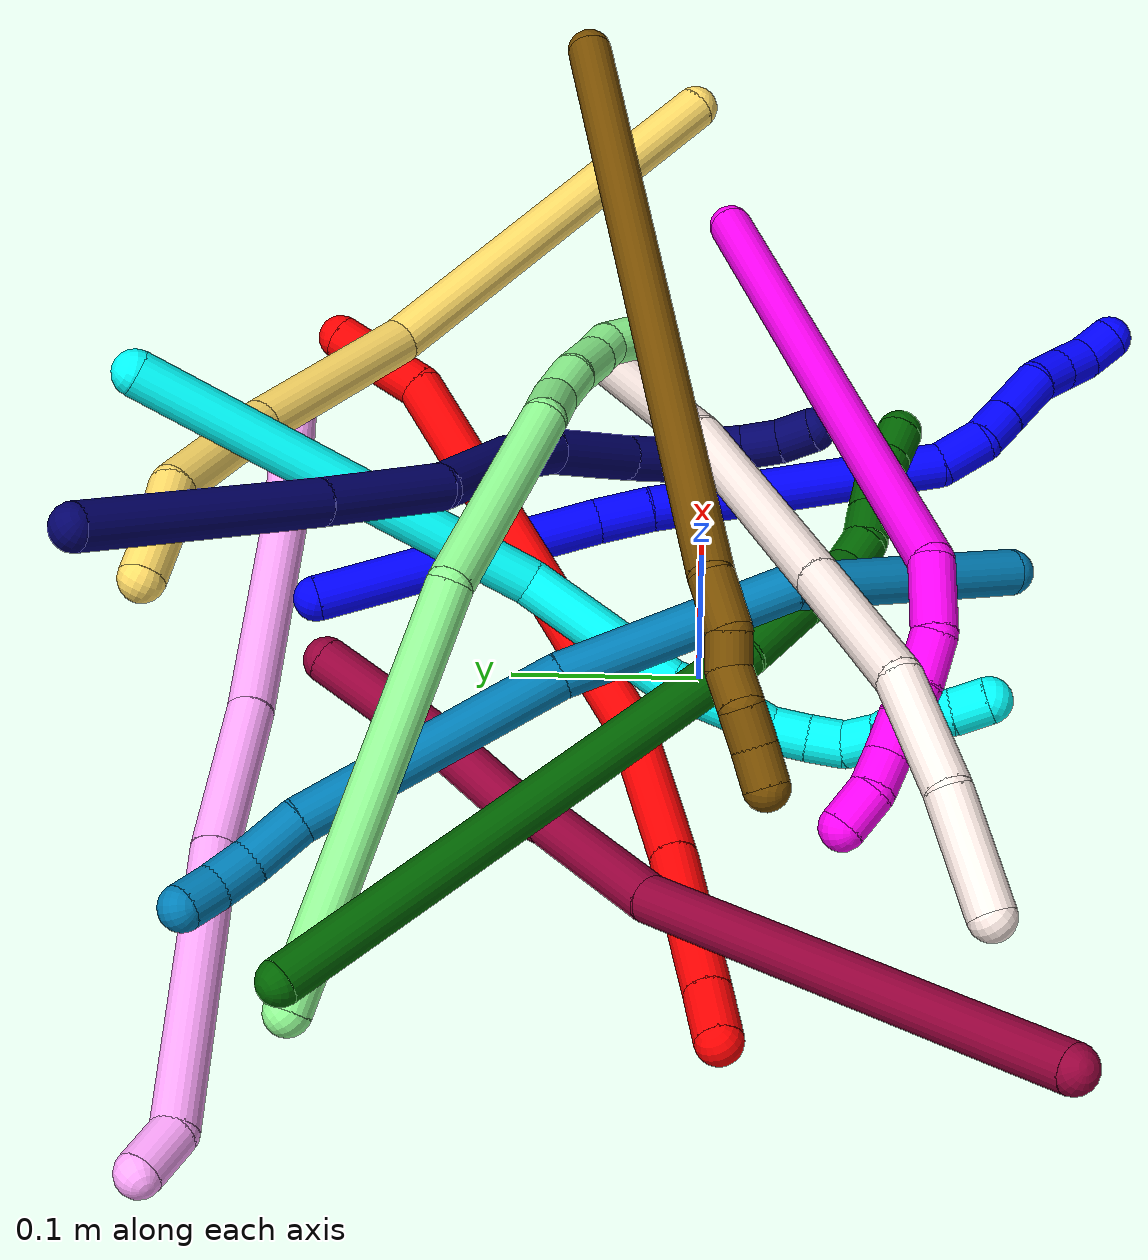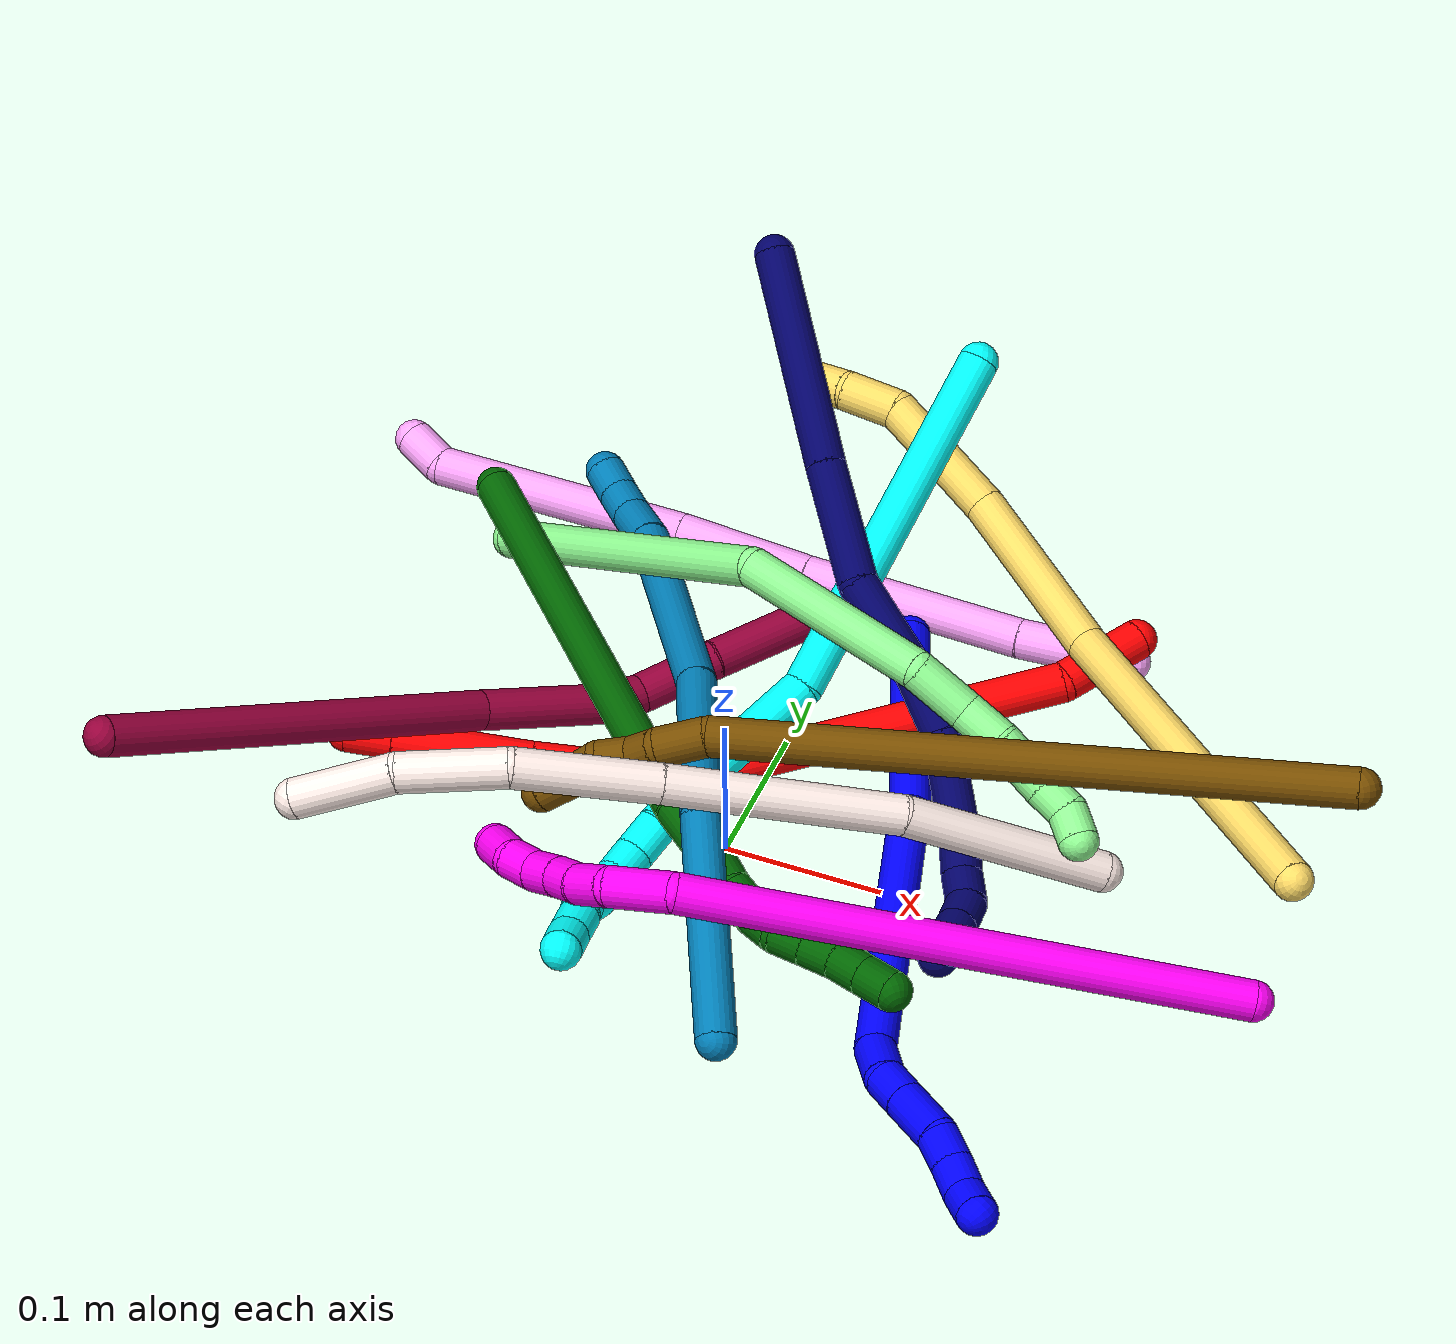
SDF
<sdf version="1.7">
 <world name="default">
  <plugin name="TubeGeneratorPlugin" filename="libtube_generator_plugin.so"/>
  <model name="photoneo_s_sensor">
   <static>1</static>
   <pose>0 0 2 1.57079 1.57079 3.14159</pose>
   <link name="link">
    <inertial><mass>0.1</mass></inertial>
    <sensor name="sensor" type="depth">
     <update_rate>30</update_rate>
     <camera>
      <horizontal_fov>1.22</horizontal_fov>
      <image><width>1920</width><height>1200</height><format>B8G8R8</format></image>
      <clip><near>0.1</near><far>4</far></clip>
      <depth_camera><output>points</output></depth_camera>
     </camera>
     <plugin name="camera_plugin" filename="libgazebo_ros_depth_camera.so">
      <baseline>0.2</baseline>
      <alwaysOn>1</alwaysOn>
      <updateRate>0.0</updateRate>
      <cameraName>camera_ir</cameraName>
      <imageTopicName>/camera/color/image_raw</imageTopicName>
      <cameraInfoTopicName>/camera/color/camera_info</cameraInfoTopicName>
      <depthImageTopicName>/camera/depth/image_raw</depthImageTopicName>
      <depthImageCameraInfoTopicName>/camera/depth/camera_info</depthImageCameraInfoTopicName>
      <pointCloudTopicName>/camera/depth/points</pointCloudTopicName>
      <frameName>fr_optical</frameName>
      <pointCloudCutoff>0.1</pointCloudCutoff>
      <pointCloudCutoffMax>2.0</pointCloudCutoffMax>
      <distortionK1>0</distortionK1>
      <distortionK2>0</distortionK2>
      <distortionK3>0</distortionK3>
      <distortionT1>0</distortionT1>
      <distortionT2>0</distortionT2>
      <CxPrime>0</CxPrime>
      <Cx>0</Cx>
      <Cy>0</Cy>
      <focalLength>0</focalLength>
      <hackBaseline>0</hackBaseline>
     </plugin>
    </sensor>
   </link>
  </model>
  <gravity>0 0 -9.8</gravity>
  <magnetic_field>6e-06 2.3e-05 -4.2e-05</magnetic_field>
  <atmosphere type="adiabatic"/>
  <physics name="default_physics" default="0" type="ode">
   <max_step_size>0.003</max_step_size>
   <real_time_factor>1</real_time_factor>
   <real_time_update_rate>1000</real_time_update_rate>
   <max_contacts>10000</max_contacts>
   <ode>
    <solver>
     <type>quick</type>
     <iters>100</iters>
     <sor>1.3</sor>
     <use_dynamic_moi_rescaling>0</use_dynamic_moi_rescaling>
    </solver>
    <constraints>
     <contact_max_correcting_vel>0</contact_max_correcting_vel>
     <contact_surface_layer>0.001</contact_surface_layer>
     <cfm>0</cfm>
     <erp>0.2</erp>
    </constraints>
   </ode>
  </physics>
  <scene><ambient>0.4 0.4 0.4 1</ambient><background>0.7 0.7 0.7 1</background><shadows>0</shadows></scene>
  <audio><device>default</device></audio>
  <spherical_coordinates>
   <surface_model>EARTH_WGS84</surface_model>
   <latitude_deg>0</latitude_deg>
   <longitude_deg>0</longitude_deg>
   <elevation>0</elevation>
   <heading_deg>0</heading_deg>
  </spherical_coordinates>
  <model name="bin">
   <static>1</static>
   <link name="bottom">
    <collision name="collision-bottom">
     <pose>0 0 -0.01 0 -0 0</pose>
     <geometry><box><size>0.8 0.6 0.02</size></box></geometry>
     <surface>
      <friction><ode><mu>100</mu><mu2>100</mu2></ode></friction>
      <contact><collide_bitmask>65535</collide_bitmask></contact>
     </surface>
    </collision>
   </link>
   <link name="west_wall">
    <collision name="collision-west_wall">
     <pose>-0.41 0 0.1 0 -0 0</pose>
     <geometry><box><size>0.02 0.6 0.2</size></box></geometry>
     <surface>
      <friction><ode><mu>100</mu><mu2>100</mu2></ode></friction>
      <contact><collide_bitmask>65535</collide_bitmask></contact>
     </surface>
    </collision>
   </link>
   <link name="east_wall">
    <collision name="collision-east_wall">
     <pose>0.41 0 0.1 0 -0 0</pose>
     <geometry><box><size>0.02 0.6 0.2</size></box></geometry>
     <surface>
      <friction><ode><mu>100</mu><mu2>100</mu2></ode></friction>
      <contact><collide_bitmask>65535</collide_bitmask></contact>
     </surface>
    </collision>
   </link>
   <link name="south_wall">
    <collision name="collision-south_wall">
     <pose>0 -0.31 0.1 0 -0 0</pose>
     <geometry><box><size>0.8 0.02 0.2</size></box></geometry>
     <surface>
      <friction><ode><mu>100</mu><mu2>100</mu2></ode></friction>
      <contact><collide_bitmask>65535</collide_bitmask></contact>
     </surface>
    </collision>
   </link>
   <link name="north_wall">
    <collision name="collision-north_wall">
     <pose>0 0.31 0.1 0 -0 0</pose>
     <geometry><box><size>0.8 0.02 0.2</size></box></geometry>
     <surface>
      <friction><ode><mu>100</mu><mu2>100</mu2></ode></friction>
      <contact><collide_bitmask>65535</collide_bitmask></contact>
     </surface>
    </collision>
   </link>
  </model>
  <model name="1">
   <static>0</static>
   <link name="1">
    <collision name="collision-cylinder-e_1_1_4">
     <pose>0.009369 -0.051583 0.060168 0.708725 0.117675 0.043581</pose>
     <geometry><cylinder><radius>0.0125</radius><length>0.15961</length></cylinder></geometry>
     <surface>
      <friction><ode><mu>1.16</mu><mu2>1.16</mu2><slip1>0</slip1><slip2>0</slip2></ode></friction>
      <contact><ode><kp>1e+06</kp><kd>1</kd><max_vel>0</max_vel><min_depth>0.001</min_depth></ode></contact>
     </surface>
    </collision>
    <visual name="visual-cylinder-e_1_1_4">
     <pose>0.009369 -0.051583 0.060168 0.708725 0.117675 0.043581</pose>
     <geometry><cylinder><radius>0.0125</radius><length>0.15961</length></cylinder></geometry>
     <material><ambient>0 0 1 1</ambient></material>
    </visual>
    <collision name="collision-cylinder-e_2_4_5">
     <pose>0.021256 -0.111806 0.132541 0.616037 0.166754 0.053162</pose>
     <geometry><cylinder><radius>0.0125</radius><length>0.030326</length></cylinder></geometry>
     <surface>
      <friction><ode><mu>1.16</mu><mu2>1.16</mu2><slip1>0</slip1><slip2>0</slip2></ode></friction>
      <contact><ode><kp>1e+06</kp><kd>1</kd><max_vel>0</max_vel><min_depth>0.001</min_depth></ode></contact>
     </surface>
    </collision>
    <visual name="visual-cylinder-e_2_4_5">
     <pose>0.021256 -0.111806 0.132541 0.616037 0.166754 0.053162</pose>
     <geometry><cylinder><radius>0.0125</radius><length>0.030326</length></cylinder></geometry>
     <material><ambient>0 0 1 1</ambient></material>
    </visual>
    <collision name="collision-cylinder-e_3_5_6">
     <pose>0.029131 -0.167474 0.212878 0.604143 0.06464 0.020149</pose>
     <geometry><cylinder><radius>0.0125</radius><length>0.16592</length></cylinder></geometry>
     <surface>
      <friction><ode><mu>1.16</mu><mu2>1.16</mu2><slip1>0</slip1><slip2>0</slip2></ode></friction>
      <contact><ode><kp>1e+06</kp><kd>1</kd><max_vel>0</max_vel><min_depth>0.001</min_depth></ode></contact>
     </surface>
    </collision>
    <visual name="visual-cylinder-e_3_5_6">
     <pose>0.029131 -0.167474 0.212878 0.604143 0.06464 0.020149</pose>
     <geometry><cylinder><radius>0.0125</radius><length>0.16592</length></cylinder></geometry>
     <material><ambient>0 0 1 1</ambient></material>
    </visual>
    <collision name="collision-cylinder-e_4_6_7">
     <pose>0.038065 -0.225424 0.289294 0.921947 0.255109 0.127223</pose>
     <geometry><cylinder><radius>0.0125</radius><length>0.028333</length></cylinder></geometry>
     <surface>
      <friction><ode><mu>1.16</mu><mu2>1.16</mu2><slip1>0</slip1><slip2>0</slip2></ode></friction>
      <contact><ode><kp>1e+06</kp><kd>1</kd><max_vel>0</max_vel><min_depth>0.001</min_depth></ode></contact>
     </surface>
    </collision>
    <visual name="visual-cylinder-e_4_6_7">
     <pose>0.038065 -0.225424 0.289294 0.921947 0.255109 0.127223</pose>
     <geometry><cylinder><radius>0.0125</radius><length>0.028333</length></cylinder></geometry>
     <material><ambient>0 0 1 1</ambient></material>
    </visual>
    <collision name="collision-cylinder-e_5_7_8">
     <pose>0.042715 -0.246571 0.300611 1.28237 0.100468 0.075016</pose>
     <geometry><cylinder><radius>0.0125</radius><length>0.021439</length></cylinder></geometry>
     <surface>
      <friction><ode><mu>1.16</mu><mu2>1.16</mu2><slip1>0</slip1><slip2>0</slip2></ode></friction>
      <contact><ode><kp>1e+06</kp><kd>1</kd><max_vel>0</max_vel><min_depth>0.001</min_depth></ode></contact>
     </surface>
    </collision>
    <visual name="visual-cylinder-e_5_7_8">
     <pose>0.042715 -0.246571 0.300611 1.28237 0.100468 0.075016</pose>
     <geometry><cylinder><radius>0.0125</radius><length>0.021439</length></cylinder></geometry>
     <material><ambient>0 0 1 1</ambient></material>
    </visual>
    <collision name="collision-cylinder-e_6_8_9">
     <pose>0.045321 -0.272715 0.308136 1.2958 0.092292 0.069876</pose>
     <geometry><cylinder><radius>0.0125</radius><length>0.033223</length></cylinder></geometry>
     <surface>
      <friction><ode><mu>1.16</mu><mu2>1.16</mu2><slip1>0</slip1><slip2>0</slip2></ode></friction>
      <contact><ode><kp>1e+06</kp><kd>1</kd><max_vel>0</max_vel><min_depth>0.001</min_depth></ode></contact>
     </surface>
    </collision>
    <visual name="visual-cylinder-e_6_8_9">
     <pose>0.045321 -0.272715 0.308136 1.2958 0.092292 0.069876</pose>
     <geometry><cylinder><radius>0.0125</radius><length>0.033223</length></cylinder></geometry>
     <material><ambient>0 0 1 1</ambient></material>
    </visual>
    <collision name="collision-cylinder-e_7_9_10">
     <pose>0.045185 -0.297734 0.317002 1.12268 -0.163666 -0.103056</pose>
     <geometry><cylinder><radius>0.0125</radius><length>0.020468</length></cylinder></geometry>
     <surface>
      <friction><ode><mu>1.16</mu><mu2>1.16</mu2><slip1>0</slip1><slip2>0</slip2></ode></friction>
      <contact><ode><kp>1e+06</kp><kd>1</kd><max_vel>0</max_vel><min_depth>0.001</min_depth></ode></contact>
     </surface>
    </collision>
    <visual name="visual-cylinder-e_7_9_10">
     <pose>0.045185 -0.297734 0.317002 1.12268 -0.163666 -0.103056</pose>
     <geometry><cylinder><radius>0.0125</radius><length>0.020468</length></cylinder></geometry>
     <material><ambient>0 0 1 1</ambient></material>
    </visual>
    <collision name="collision-cylinder-e_8_10_11">
     <pose>0.042504 -0.315732 0.326353 1.06082 -0.099034 -0.058111</pose>
     <geometry><cylinder><radius>0.0125</radius><length>0.02049</length></cylinder></geometry>
     <surface>
      <friction><ode><mu>1.16</mu><mu2>1.16</mu2><slip1>0</slip1><slip2>0</slip2></ode></friction>
      <contact><ode><kp>1e+06</kp><kd>1</kd><max_vel>0</max_vel><min_depth>0.001</min_depth></ode></contact>
     </surface>
    </collision>
    <visual name="visual-cylinder-e_8_10_11">
     <pose>0.042504 -0.315732 0.326353 1.06082 -0.099034 -0.058111</pose>
     <geometry><cylinder><radius>0.0125</radius><length>0.02049</length></cylinder></geometry>
     <material><ambient>0 0 1 1</ambient></material>
    </visual>
    <collision name="collision-cylinder-e_9_11_2">
     <pose>0.044214 -0.333122 0.336061 1.06251 0.273032 0.161089</pose>
     <geometry><cylinder><radius>0.0125</radius><length>0.020191</length></cylinder></geometry>
     <surface>
      <friction><ode><mu>1.16</mu><mu2>1.16</mu2><slip1>0</slip1><slip2>0</slip2></ode></friction>
      <contact><ode><kp>1e+06</kp><kd>1</kd><max_vel>0</max_vel><min_depth>0.001</min_depth></ode></contact>
     </surface>
    </collision>
    <visual name="visual-cylinder-e_9_11_2">
     <pose>0.044214 -0.333122 0.336061 1.06251 0.273032 0.161089</pose>
     <geometry><cylinder><radius>0.0125</radius><length>0.020191</length></cylinder></geometry>
     <material><ambient>0 0 1 1</ambient></material>
    </visual>
    <collision name="collision-sphere-2">
     <pose>0.046936 -0.341615 0.340793 0 -0 0</pose>
     <geometry><sphere><radius>0.0125</radius></sphere></geometry>
     <surface>
      <friction><ode><mu>1.16</mu><mu2>1.16</mu2><slip1>0</slip1><slip2>0</slip2></ode></friction>
      <contact><ode><kp>1e+06</kp><kd>1</kd><max_vel>0</max_vel><min_depth>0.001</min_depth></ode></contact>
     </surface>
    </collision>
    <visual name="visual-sphere-2">
     <pose>0.046936 -0.341615 0.340793 0 -0 0</pose>
     <geometry><sphere><radius>0.0125</radius></sphere></geometry>
     <material><ambient>0 0 1 1</ambient></material>
    </visual>
    <collision name="collision-sphere-11">
     <pose>0.041491 -0.324629 0.33133 0 -0 0</pose>
     <geometry><sphere><radius>0.0125</radius></sphere></geometry>
     <surface>
      <friction><ode><mu>1.16</mu><mu2>1.16</mu2><slip1>0</slip1><slip2>0</slip2></ode></friction>
      <contact><ode><kp>1e+06</kp><kd>1</kd><max_vel>0</max_vel><min_depth>0.001</min_depth></ode></contact>
     </surface>
    </collision>
    <visual name="visual-sphere-11">
     <pose>0.041491 -0.324629 0.33133 0 -0 0</pose>
     <geometry><sphere><radius>0.0125</radius></sphere></geometry>
     <material><ambient>0 0 1 1</ambient></material>
    </visual>
    <collision name="collision-sphere-10">
     <pose>0.043517 -0.306835 0.321377 0 -0 0</pose>
     <geometry><sphere><radius>0.0125</radius></sphere></geometry>
     <surface>
      <friction><ode><mu>1.16</mu><mu2>1.16</mu2><slip1>0</slip1><slip2>0</slip2></ode></friction>
      <contact><ode><kp>1e+06</kp><kd>1</kd><max_vel>0</max_vel><min_depth>0.001</min_depth></ode></contact>
     </surface>
    </collision>
    <visual name="visual-sphere-10">
     <pose>0.043517 -0.306835 0.321377 0 -0 0</pose>
     <geometry><sphere><radius>0.0125</radius></sphere></geometry>
     <material><ambient>0 0 1 1</ambient></material>
    </visual>
    <collision name="collision-sphere-9">
     <pose>0.046852 -0.288634 0.312627 0 -0 0</pose>
     <geometry><sphere><radius>0.0125</radius></sphere></geometry>
     <surface>
      <friction><ode><mu>1.16</mu><mu2>1.16</mu2><slip1>0</slip1><slip2>0</slip2></ode></friction>
      <contact><ode><kp>1e+06</kp><kd>1</kd><max_vel>0</max_vel><min_depth>0.001</min_depth></ode></contact>
     </surface>
    </collision>
    <visual name="visual-sphere-9">
     <pose>0.046852 -0.288634 0.312627 0 -0 0</pose>
     <geometry><sphere><radius>0.0125</radius></sphere></geometry>
     <material><ambient>0 0 1 1</ambient></material>
    </visual>
    <collision name="collision-sphere-4">
     <pose>0.018739 -0.103167 0.120337 0 -0 0</pose>
     <geometry><sphere><radius>0.0125</radius></sphere></geometry>
     <surface>
      <friction><ode><mu>1.16</mu><mu2>1.16</mu2><slip1>0</slip1><slip2>0</slip2></ode></friction>
      <contact><ode><kp>1e+06</kp><kd>1</kd><max_vel>0</max_vel><min_depth>0.001</min_depth></ode></contact>
     </surface>
    </collision>
    <visual name="visual-sphere-4">
     <pose>0.018739 -0.103167 0.120337 0 -0 0</pose>
     <geometry><sphere><radius>0.0125</radius></sphere></geometry>
     <material><ambient>0 0 1 1</ambient></material>
    </visual>
    <collision name="collision-sphere-1">
     <geometry><sphere><radius>0.0125</radius></sphere></geometry>
     <surface>
      <friction><ode><mu>1.16</mu><mu2>1.16</mu2><slip1>0</slip1><slip2>0</slip2></ode></friction>
      <contact><ode><kp>1e+06</kp><kd>1</kd><max_vel>0</max_vel><min_depth>0.001</min_depth></ode></contact>
     </surface>
    </collision>
    <visual name="visual-sphere-1">
     <geometry><sphere><radius>0.0125</radius></sphere></geometry>
     <material><ambient>0 0 1 1</ambient></material>
    </visual>
    <collision name="collision-sphere-8">
     <pose>0.04379 -0.256795 0.303644 0 -0 0</pose>
     <geometry><sphere><radius>0.0125</radius></sphere></geometry>
     <surface>
      <friction><ode><mu>1.16</mu><mu2>1.16</mu2><slip1>0</slip1><slip2>0</slip2></ode></friction>
      <contact><ode><kp>1e+06</kp><kd>1</kd><max_vel>0</max_vel><min_depth>0.001</min_depth></ode></contact>
     </surface>
    </collision>
    <visual name="visual-sphere-8">
     <pose>0.04379 -0.256795 0.303644 0 -0 0</pose>
     <geometry><sphere><radius>0.0125</radius></sphere></geometry>
     <material><ambient>0 0 1 1</ambient></material>
    </visual>
    <collision name="collision-sphere-5">
     <pose>0.023773 -0.120446 0.144745 0 -0 0</pose>
     <geometry><sphere><radius>0.0125</radius></sphere></geometry>
     <surface>
      <friction><ode><mu>1.16</mu><mu2>1.16</mu2><slip1>0</slip1><slip2>0</slip2></ode></friction>
      <contact><ode><kp>1e+06</kp><kd>1</kd><max_vel>0</max_vel><min_depth>0.001</min_depth></ode></contact>
     </surface>
    </collision>
    <visual name="visual-sphere-5">
     <pose>0.023773 -0.120446 0.144745 0 -0 0</pose>
     <geometry><sphere><radius>0.0125</radius></sphere></geometry>
     <material><ambient>0 0 1 1</ambient></material>
    </visual>
    <collision name="collision-sphere-6">
     <pose>0.03449 -0.214501 0.28101 0 -0 0</pose>
     <geometry><sphere><radius>0.0125</radius></sphere></geometry>
     <surface>
      <friction><ode><mu>1.16</mu><mu2>1.16</mu2><slip1>0</slip1><slip2>0</slip2></ode></friction>
      <contact><ode><kp>1e+06</kp><kd>1</kd><max_vel>0</max_vel><min_depth>0.001</min_depth></ode></contact>
     </surface>
    </collision>
    <visual name="visual-sphere-6">
     <pose>0.03449 -0.214501 0.28101 0 -0 0</pose>
     <geometry><sphere><radius>0.0125</radius></sphere></geometry>
     <material><ambient>0 0 1 1</ambient></material>
    </visual>
    <collision name="collision-sphere-7">
     <pose>0.04164 -0.236346 0.297577 0 -0 0</pose>
     <geometry><sphere><radius>0.0125</radius></sphere></geometry>
     <surface>
      <friction><ode><mu>1.16</mu><mu2>1.16</mu2><slip1>0</slip1><slip2>0</slip2></ode></friction>
      <contact><ode><kp>1e+06</kp><kd>1</kd><max_vel>0</max_vel><min_depth>0.001</min_depth></ode></contact>
     </surface>
    </collision>
    <visual name="visual-sphere-7">
     <pose>0.04164 -0.236346 0.297577 0 -0 0</pose>
     <geometry><sphere><radius>0.0125</radius></sphere></geometry>
     <material><ambient>0 0 1 1</ambient></material>
    </visual>
    <inertial>
     <pose>0.026324 -0.158868 0.187566 0 -0 0</pose>
     <mass>0.5</mass>
     <inertia>
      <ixx>0.000773</ixx>
      <ixy>0</ixy>
      <ixz>0</ixz>
      <iyy>0.000587</iyy>
      <iyz>0</iyz>
      <izz>0.000416</izz>
     </inertia>
    </inertial>
   </link>
   <pose>0.040309 0.20731 0.011522 2.86304 -1.46933 -1.63845</pose>
  </model>
  <model name="2">
   <static>0</static>
   <link name="2">
    <collision name="collision-cylinder-e_1_1_4">
     <pose>-0.014062 -0.019936 -0.013177 2.15486 -0.531861 -0.937749</pose>
     <geometry><cylinder><radius>0.0125</radius><length>0.055455</length></cylinder></geometry>
     <surface>
      <friction><ode><mu>1.16</mu><mu2>1.16</mu2><slip1>0</slip1><slip2>0</slip2></ode></friction>
      <contact><ode><kp>1e+06</kp><kd>1</kd><max_vel>0</max_vel><min_depth>0.001</min_depth></ode></contact>
     </surface>
    </collision>
    <visual name="visual-cylinder-e_1_1_4">
     <pose>-0.014062 -0.019936 -0.013177 2.15486 -0.531861 -0.937749</pose>
     <geometry><cylinder><radius>0.0125</radius><length>0.055455</length></cylinder></geometry>
     <material><ambient>1 0 0 1</ambient></material>
    </visual>
    <collision name="collision-cylinder-e_2_4_5">
     <pose>-0.123648 -0.088109 -0.081205 2.42026 -0.917981 -1.83781</pose>
     <geometry><cylinder><radius>0.0125</radius><length>0.240502</length></cylinder></geometry>
     <surface>
      <friction><ode><mu>1.16</mu><mu2>1.16</mu2><slip1>0</slip1><slip2>0</slip2></ode></friction>
      <contact><ode><kp>1e+06</kp><kd>1</kd><max_vel>0</max_vel><min_depth>0.001</min_depth></ode></contact>
     </surface>
    </collision>
    <visual name="visual-cylinder-e_2_4_5">
     <pose>-0.123648 -0.088109 -0.081205 2.42026 -0.917981 -1.83781</pose>
     <geometry><cylinder><radius>0.0125</radius><length>0.240502</length></cylinder></geometry>
     <material><ambient>1 0 0 1</ambient></material>
    </visual>
    <collision name="collision-cylinder-e_3_5_6">
     <pose>-0.261452 -0.147818 -0.14336 2.13776 -1.25957 -1.85073</pose>
     <geometry><cylinder><radius>0.0125</radius><length>0.088827</length></cylinder></geometry>
     <surface>
      <friction><ode><mu>1.16</mu><mu2>1.16</mu2><slip1>0</slip1><slip2>0</slip2></ode></friction>
      <contact><ode><kp>1e+06</kp><kd>1</kd><max_vel>0</max_vel><min_depth>0.001</min_depth></ode></contact>
     </surface>
    </collision>
    <visual name="visual-cylinder-e_3_5_6">
     <pose>-0.261452 -0.147818 -0.14336 2.13776 -1.25957 -1.85073</pose>
     <geometry><cylinder><radius>0.0125</radius><length>0.088827</length></cylinder></geometry>
     <material><ambient>1 0 0 1</ambient></material>
    </visual>
    <collision name="collision-cylinder-e_4_6_7">
     <pose>-0.345279 -0.168411 -0.156673 2.15333 -1.31374 -1.922</pose>
     <geometry><cylinder><radius>0.0125</radius><length>0.085916</length></cylinder></geometry>
     <surface>
      <friction><ode><mu>1.16</mu><mu2>1.16</mu2><slip1>0</slip1><slip2>0</slip2></ode></friction>
      <contact><ode><kp>1e+06</kp><kd>1</kd><max_vel>0</max_vel><min_depth>0.001</min_depth></ode></contact>
     </surface>
    </collision>
    <visual name="visual-cylinder-e_4_6_7">
     <pose>-0.345279 -0.168411 -0.156673 2.15333 -1.31374 -1.922</pose>
     <geometry><cylinder><radius>0.0125</radius><length>0.085916</length></cylinder></geometry>
     <material><ambient>1 0 0 1</ambient></material>
    </visual>
    <collision name="collision-cylinder-e_5_7_2">
     <pose>-0.401028 -0.180403 -0.164839 2.2152 -1.32303 -2.00083</pose>
     <geometry><cylinder><radius>0.0125</radius><length>0.0293</length></cylinder></geometry>
     <surface>
      <friction><ode><mu>1.16</mu><mu2>1.16</mu2><slip1>0</slip1><slip2>0</slip2></ode></friction>
      <contact><ode><kp>1e+06</kp><kd>1</kd><max_vel>0</max_vel><min_depth>0.001</min_depth></ode></contact>
     </surface>
    </collision>
    <visual name="visual-cylinder-e_5_7_2">
     <pose>-0.401028 -0.180403 -0.164839 2.2152 -1.32303 -2.00083</pose>
     <geometry><cylinder><radius>0.0125</radius><length>0.0293</length></cylinder></geometry>
     <material><ambient>1 0 0 1</ambient></material>
    </visual>
    <collision name="collision-sphere-2">
     <pose>-0.415231 -0.183275 -0.166997 0 -0 0</pose>
     <geometry><sphere><radius>0.0125</radius></sphere></geometry>
     <surface>
      <friction><ode><mu>1.16</mu><mu2>1.16</mu2><slip1>0</slip1><slip2>0</slip2></ode></friction>
      <contact><ode><kp>1e+06</kp><kd>1</kd><max_vel>0</max_vel><min_depth>0.001</min_depth></ode></contact>
     </surface>
    </collision>
    <visual name="visual-sphere-2">
     <pose>-0.415231 -0.183275 -0.166997 0 -0 0</pose>
     <geometry><sphere><radius>0.0125</radius></sphere></geometry>
     <material><ambient>1 0 0 1</ambient></material>
    </visual>
    <collision name="collision-sphere-7">
     <pose>-0.386825 -0.177531 -0.162681 0 -0 0</pose>
     <geometry><sphere><radius>0.0125</radius></sphere></geometry>
     <surface>
      <friction><ode><mu>1.16</mu><mu2>1.16</mu2><slip1>0</slip1><slip2>0</slip2></ode></friction>
      <contact><ode><kp>1e+06</kp><kd>1</kd><max_vel>0</max_vel><min_depth>0.001</min_depth></ode></contact>
     </surface>
    </collision>
    <visual name="visual-sphere-7">
     <pose>-0.386825 -0.177531 -0.162681 0 -0 0</pose>
     <geometry><sphere><radius>0.0125</radius></sphere></geometry>
     <material><ambient>1 0 0 1</ambient></material>
    </visual>
    <collision name="collision-sphere-6">
     <pose>-0.303732 -0.159291 -0.150664 0 -0 0</pose>
     <geometry><sphere><radius>0.0125</radius></sphere></geometry>
     <surface>
      <friction><ode><mu>1.16</mu><mu2>1.16</mu2><slip1>0</slip1><slip2>0</slip2></ode></friction>
      <contact><ode><kp>1e+06</kp><kd>1</kd><max_vel>0</max_vel><min_depth>0.001</min_depth></ode></contact>
     </surface>
    </collision>
    <visual name="visual-sphere-6">
     <pose>-0.303732 -0.159291 -0.150664 0 -0 0</pose>
     <geometry><sphere><radius>0.0125</radius></sphere></geometry>
     <material><ambient>1 0 0 1</ambient></material>
    </visual>
    <collision name="collision-sphere-5">
     <pose>-0.219173 -0.136346 -0.136055 0 -0 0</pose>
     <geometry><sphere><radius>0.0125</radius></sphere></geometry>
     <surface>
      <friction><ode><mu>1.16</mu><mu2>1.16</mu2><slip1>0</slip1><slip2>0</slip2></ode></friction>
      <contact><ode><kp>1e+06</kp><kd>1</kd><max_vel>0</max_vel><min_depth>0.001</min_depth></ode></contact>
     </surface>
    </collision>
    <visual name="visual-sphere-5">
     <pose>-0.219173 -0.136346 -0.136055 0 -0 0</pose>
     <geometry><sphere><radius>0.0125</radius></sphere></geometry>
     <material><ambient>1 0 0 1</ambient></material>
    </visual>
    <collision name="collision-sphere-1">
     <geometry><sphere><radius>0.0125</radius></sphere></geometry>
     <surface>
      <friction><ode><mu>1.16</mu><mu2>1.16</mu2><slip1>0</slip1><slip2>0</slip2></ode></friction>
      <contact><ode><kp>1e+06</kp><kd>1</kd><max_vel>0</max_vel><min_depth>0.001</min_depth></ode></contact>
     </surface>
    </collision>
    <visual name="visual-sphere-1">
     <geometry><sphere><radius>0.0125</radius></sphere></geometry>
     <material><ambient>1 0 0 1</ambient></material>
    </visual>
    <collision name="collision-sphere-4">
     <pose>-0.028123 -0.039871 -0.026355 0 -0 0</pose>
     <geometry><sphere><radius>0.0125</radius></sphere></geometry>
     <surface>
      <friction><ode><mu>1.16</mu><mu2>1.16</mu2><slip1>0</slip1><slip2>0</slip2></ode></friction>
      <contact><ode><kp>1e+06</kp><kd>1</kd><max_vel>0</max_vel><min_depth>0.001</min_depth></ode></contact>
     </surface>
    </collision>
    <visual name="visual-sphere-4">
     <pose>-0.028123 -0.039871 -0.026355 0 -0 0</pose>
     <geometry><sphere><radius>0.0125</radius></sphere></geometry>
     <material><ambient>1 0 0 1</ambient></material>
    </visual>
    <inertial>
     <pose>-0.190313 -0.110362 -0.102571 0 -0 0</pose>
     <mass>0.5</mass>
     <inertia>
      <ixx>-0.00095</ixx>
      <ixy>0</ixy>
      <ixz>0</ixz>
      <iyy>0.000194</iyy>
      <iyz>0</iyz>
      <izz>0.001549</izz>
     </inertia>
    </inertial>
   </link>
   <pose>0.187995 0.203329 0.06188 -0.38402 0.114901 -0.035967</pose>
  </model>
  <model name="3">
   <static>0</static>
   <link name="3">
    <collision name="collision-cylinder-e_1_1_4">
     <pose>-0.028143 -0.002642 -0.112125 3.11803 -0.245846 -2.95148</pose>
     <geometry><cylinder><radius>0.0125</radius><length>0.231267</length></cylinder></geometry>
     <surface>
      <friction><ode><mu>1.16</mu><mu2>1.16</mu2><slip1>0</slip1><slip2>0</slip2></ode></friction>
      <contact><ode><kp>1e+06</kp><kd>1</kd><max_vel>0</max_vel><min_depth>0.001</min_depth></ode></contact>
     </surface>
    </collision>
    <visual name="visual-cylinder-e_1_1_4">
     <pose>-0.028143 -0.002642 -0.112125 3.11803 -0.245846 -2.95148</pose>
     <geometry><cylinder><radius>0.0125</radius><length>0.231267</length></cylinder></geometry>
     <material><ambient>0.003922 1 0.996078 1</ambient></material>
    </visual>
    <collision name="collision-cylinder-e_2_4_5">
     <pose>-0.080542 -0.011814 -0.262181 2.97111 -0.562366 -2.56632</pose>
     <geometry><cylinder><radius>0.0125</radius><length>0.090988</length></cylinder></geometry>
     <surface>
      <friction><ode><mu>1.16</mu><mu2>1.16</mu2><slip1>0</slip1><slip2>0</slip2></ode></friction>
      <contact><ode><kp>1e+06</kp><kd>1</kd><max_vel>0</max_vel><min_depth>0.001</min_depth></ode></contact>
     </surface>
    </collision>
    <visual name="visual-cylinder-e_2_4_5">
     <pose>-0.080542 -0.011814 -0.262181 2.97111 -0.562366 -2.56632</pose>
     <geometry><cylinder><radius>0.0125</radius><length>0.090988</length></cylinder></geometry>
     <material><ambient>0.003922 1 0.996078 1</ambient></material>
    </visual>
    <collision name="collision-cylinder-e_3_5_6">
     <pose>-0.110775 -0.023143 -0.315104 2.83179 -0.362802 -1.73104</pose>
     <geometry><cylinder><radius>0.0125</radius><length>0.033677</length></cylinder></geometry>
     <surface>
      <friction><ode><mu>1.16</mu><mu2>1.16</mu2><slip1>0</slip1><slip2>0</slip2></ode></friction>
      <contact><ode><kp>1e+06</kp><kd>1</kd><max_vel>0</max_vel><min_depth>0.001</min_depth></ode></contact>
     </surface>
    </collision>
    <visual name="visual-cylinder-e_3_5_6">
     <pose>-0.110775 -0.023143 -0.315104 2.83179 -0.362802 -1.73104</pose>
     <geometry><cylinder><radius>0.0125</radius><length>0.033677</length></cylinder></geometry>
     <material><ambient>0.003922 1 0.996078 1</ambient></material>
    </visual>
    <collision name="collision-cylinder-e_4_6_7">
     <pose>-0.121392 -0.029242 -0.340567 3.01809 -0.414442 -2.56955</pose>
     <geometry><cylinder><radius>0.0125</radius><length>0.023053</length></cylinder></geometry>
     <surface>
      <friction><ode><mu>1.16</mu><mu2>1.16</mu2><slip1>0</slip1><slip2>0</slip2></ode></friction>
      <contact><ode><kp>1e+06</kp><kd>1</kd><max_vel>0</max_vel><min_depth>0.001</min_depth></ode></contact>
     </surface>
    </collision>
    <visual name="visual-cylinder-e_4_6_7">
     <pose>-0.121392 -0.029242 -0.340567 3.01809 -0.414442 -2.56955</pose>
     <geometry><cylinder><radius>0.0125</radius><length>0.023053</length></cylinder></geometry>
     <material><ambient>0.003922 1 0.996078 1</ambient></material>
    </visual>
    <collision name="collision-cylinder-e_5_7_8">
     <pose>-0.128687 -0.034981 -0.360083 2.6854 -0.257458 -1.01735</pose>
     <geometry><cylinder><radius>0.0125</radius><length>0.020838</length></cylinder></geometry>
     <surface>
      <friction><ode><mu>1.16</mu><mu2>1.16</mu2><slip1>0</slip1><slip2>0</slip2></ode></friction>
      <contact><ode><kp>1e+06</kp><kd>1</kd><max_vel>0</max_vel><min_depth>0.001</min_depth></ode></contact>
     </surface>
    </collision>
    <visual name="visual-cylinder-e_5_7_8">
     <pose>-0.128687 -0.034981 -0.360083 2.6854 -0.257458 -1.01735</pose>
     <geometry><cylinder><radius>0.0125</radius><length>0.020838</length></cylinder></geometry>
     <material><ambient>0.003922 1 0.996078 1</ambient></material>
    </visual>
    <collision name="collision-cylinder-e_6_8_9">
     <pose>-0.133946 -0.044326 -0.377503 2.61157 -0.262257 -0.904701</pose>
     <geometry><cylinder><radius>0.0125</radius><length>0.0201</length></cylinder></geometry>
     <surface>
      <friction><ode><mu>1.16</mu><mu2>1.16</mu2><slip1>0</slip1><slip2>0</slip2></ode></friction>
      <contact><ode><kp>1e+06</kp><kd>1</kd><max_vel>0</max_vel><min_depth>0.001</min_depth></ode></contact>
     </surface>
    </collision>
    <visual name="visual-cylinder-e_6_8_9">
     <pose>-0.133946 -0.044326 -0.377503 2.61157 -0.262257 -0.904701</pose>
     <geometry><cylinder><radius>0.0125</radius><length>0.0201</length></cylinder></geometry>
     <material><ambient>0.003922 1 0.996078 1</ambient></material>
    </visual>
    <collision name="collision-cylinder-e_7_9_10">
     <pose>-0.137749 -0.057747 -0.391048 2.11657 -0.119672 -0.212145</pose>
     <geometry><cylinder><radius>0.0125</radius><length>0.020064</length></cylinder></geometry>
     <surface>
      <friction><ode><mu>1.16</mu><mu2>1.16</mu2><slip1>0</slip1><slip2>0</slip2></ode></friction>
      <contact><ode><kp>1e+06</kp><kd>1</kd><max_vel>0</max_vel><min_depth>0.001</min_depth></ode></contact>
     </surface>
    </collision>
    <visual name="visual-cylinder-e_7_9_10">
     <pose>-0.137749 -0.057747 -0.391048 2.11657 -0.119672 -0.212145</pose>
     <geometry><cylinder><radius>0.0125</radius><length>0.020064</length></cylinder></geometry>
     <material><ambient>0.003922 1 0.996078 1</ambient></material>
    </visual>
    <collision name="collision-cylinder-e_8_10_11">
     <pose>-0.136866 -0.0747 -0.401167 2.10112 0.2095 0.363002</pose>
     <geometry><cylinder><radius>0.0125</radius><length>0.020005</length></cylinder></geometry>
     <surface>
      <friction><ode><mu>1.16</mu><mu2>1.16</mu2><slip1>0</slip1><slip2>0</slip2></ode></friction>
      <contact><ode><kp>1e+06</kp><kd>1</kd><max_vel>0</max_vel><min_depth>0.001</min_depth></ode></contact>
     </surface>
    </collision>
    <visual name="visual-cylinder-e_8_10_11">
     <pose>-0.136866 -0.0747 -0.401167 2.10112 0.2095 0.363002</pose>
     <geometry><cylinder><radius>0.0125</radius><length>0.020005</length></cylinder></geometry>
     <material><ambient>0.003922 1 0.996078 1</ambient></material>
    </visual>
    <collision name="collision-cylinder-e_9_11_12">
     <pose>-0.134669 -0.089691 -0.413671 2.42721 0.011711 0.031379</pose>
     <geometry><cylinder><radius>0.0125</radius><length>0.020001</length></cylinder></geometry>
     <surface>
      <friction><ode><mu>1.16</mu><mu2>1.16</mu2><slip1>0</slip1><slip2>0</slip2></ode></friction>
      <contact><ode><kp>1e+06</kp><kd>1</kd><max_vel>0</max_vel><min_depth>0.001</min_depth></ode></contact>
     </surface>
    </collision>
    <visual name="visual-cylinder-e_9_11_12">
     <pose>-0.134669 -0.089691 -0.413671 2.42721 0.011711 0.031379</pose>
     <geometry><cylinder><radius>0.0125</radius><length>0.020001</length></cylinder></geometry>
     <material><ambient>0.003922 1 0.996078 1</ambient></material>
    </visual>
    <collision name="collision-cylinder-e_10_12_2">
     <pose>-0.133562 -0.103883 -0.427605 2.26648 0.099101 0.211231</pose>
     <geometry><cylinder><radius>0.0125</radius><length>0.020006</length></cylinder></geometry>
     <surface>
      <friction><ode><mu>1.16</mu><mu2>1.16</mu2><slip1>0</slip1><slip2>0</slip2></ode></friction>
      <contact><ode><kp>1e+06</kp><kd>1</kd><max_vel>0</max_vel><min_depth>0.001</min_depth></ode></contact>
     </surface>
    </collision>
    <visual name="visual-cylinder-e_10_12_2">
     <pose>-0.133562 -0.103883 -0.427605 2.26648 0.099101 0.211231</pose>
     <geometry><cylinder><radius>0.0125</radius><length>0.020006</length></cylinder></geometry>
     <material><ambient>0.003922 1 0.996078 1</ambient></material>
    </visual>
    <collision name="collision-sphere-2">
     <pose>-0.132573 -0.111524 -0.433984 0 -0 0</pose>
     <geometry><sphere><radius>0.0125</radius></sphere></geometry>
     <surface>
      <friction><ode><mu>1.16</mu><mu2>1.16</mu2><slip1>0</slip1><slip2>0</slip2></ode></friction>
      <contact><ode><kp>1e+06</kp><kd>1</kd><max_vel>0</max_vel><min_depth>0.001</min_depth></ode></contact>
     </surface>
    </collision>
    <visual name="visual-sphere-2">
     <pose>-0.132573 -0.111524 -0.433984 0 -0 0</pose>
     <geometry><sphere><radius>0.0125</radius></sphere></geometry>
     <material><ambient>0.003922 1 0.996078 1</ambient></material>
    </visual>
    <collision name="collision-sphere-12">
     <pose>-0.134552 -0.096243 -0.421225 0 -0 0</pose>
     <geometry><sphere><radius>0.0125</radius></sphere></geometry>
     <surface>
      <friction><ode><mu>1.16</mu><mu2>1.16</mu2><slip1>0</slip1><slip2>0</slip2></ode></friction>
      <contact><ode><kp>1e+06</kp><kd>1</kd><max_vel>0</max_vel><min_depth>0.001</min_depth></ode></contact>
     </surface>
    </collision>
    <visual name="visual-sphere-12">
     <pose>-0.134552 -0.096243 -0.421225 0 -0 0</pose>
     <geometry><sphere><radius>0.0125</radius></sphere></geometry>
     <material><ambient>0.003922 1 0.996078 1</ambient></material>
    </visual>
    <collision name="collision-sphere-11">
     <pose>-0.134786 -0.08314 -0.406116 0 -0 0</pose>
     <geometry><sphere><radius>0.0125</radius></sphere></geometry>
     <surface>
      <friction><ode><mu>1.16</mu><mu2>1.16</mu2><slip1>0</slip1><slip2>0</slip2></ode></friction>
      <contact><ode><kp>1e+06</kp><kd>1</kd><max_vel>0</max_vel><min_depth>0.001</min_depth></ode></contact>
     </surface>
    </collision>
    <visual name="visual-sphere-11">
     <pose>-0.134786 -0.08314 -0.406116 0 -0 0</pose>
     <geometry><sphere><radius>0.0125</radius></sphere></geometry>
     <material><ambient>0.003922 1 0.996078 1</ambient></material>
    </visual>
    <collision name="collision-sphere-10">
     <pose>-0.138947 -0.06626 -0.396218 0 -0 0</pose>
     <geometry><sphere><radius>0.0125</radius></sphere></geometry>
     <surface>
      <friction><ode><mu>1.16</mu><mu2>1.16</mu2><slip1>0</slip1><slip2>0</slip2></ode></friction>
      <contact><ode><kp>1e+06</kp><kd>1</kd><max_vel>0</max_vel><min_depth>0.001</min_depth></ode></contact>
     </surface>
    </collision>
    <visual name="visual-sphere-10">
     <pose>-0.138947 -0.06626 -0.396218 0 -0 0</pose>
     <geometry><sphere><radius>0.0125</radius></sphere></geometry>
     <material><ambient>0.003922 1 0.996078 1</ambient></material>
    </visual>
    <collision name="collision-sphere-9">
     <pose>-0.136551 -0.049234 -0.385878 0 -0 0</pose>
     <geometry><sphere><radius>0.0125</radius></sphere></geometry>
     <surface>
      <friction><ode><mu>1.16</mu><mu2>1.16</mu2><slip1>0</slip1><slip2>0</slip2></ode></friction>
      <contact><ode><kp>1e+06</kp><kd>1</kd><max_vel>0</max_vel><min_depth>0.001</min_depth></ode></contact>
     </surface>
    </collision>
    <visual name="visual-sphere-9">
     <pose>-0.136551 -0.049234 -0.385878 0 -0 0</pose>
     <geometry><sphere><radius>0.0125</radius></sphere></geometry>
     <material><ambient>0.003922 1 0.996078 1</ambient></material>
    </visual>
    <collision name="collision-sphere-4">
     <pose>-0.056285 -0.005284 -0.224251 0 -0 0</pose>
     <geometry><sphere><radius>0.0125</radius></sphere></geometry>
     <surface>
      <friction><ode><mu>1.16</mu><mu2>1.16</mu2><slip1>0</slip1><slip2>0</slip2></ode></friction>
      <contact><ode><kp>1e+06</kp><kd>1</kd><max_vel>0</max_vel><min_depth>0.001</min_depth></ode></contact>
     </surface>
    </collision>
    <visual name="visual-sphere-4">
     <pose>-0.056285 -0.005284 -0.224251 0 -0 0</pose>
     <geometry><sphere><radius>0.0125</radius></sphere></geometry>
     <material><ambient>0.003922 1 0.996078 1</ambient></material>
    </visual>
    <collision name="collision-sphere-1">
     <geometry><sphere><radius>0.0125</radius></sphere></geometry>
     <surface>
      <friction><ode><mu>1.16</mu><mu2>1.16</mu2><slip1>0</slip1><slip2>0</slip2></ode></friction>
      <contact><ode><kp>1e+06</kp><kd>1</kd><max_vel>0</max_vel><min_depth>0.001</min_depth></ode></contact>
     </surface>
    </collision>
    <visual name="visual-sphere-1">
     <geometry><sphere><radius>0.0125</radius></sphere></geometry>
     <material><ambient>0.003922 1 0.996078 1</ambient></material>
    </visual>
    <collision name="collision-sphere-8">
     <pose>-0.13134 -0.039419 -0.369128 0 -0 0</pose>
     <geometry><sphere><radius>0.0125</radius></sphere></geometry>
     <surface>
      <friction><ode><mu>1.16</mu><mu2>1.16</mu2><slip1>0</slip1><slip2>0</slip2></ode></friction>
      <contact><ode><kp>1e+06</kp><kd>1</kd><max_vel>0</max_vel><min_depth>0.001</min_depth></ode></contact>
     </surface>
    </collision>
    <visual name="visual-sphere-8">
     <pose>-0.13134 -0.039419 -0.369128 0 -0 0</pose>
     <geometry><sphere><radius>0.0125</radius></sphere></geometry>
     <material><ambient>0.003922 1 0.996078 1</ambient></material>
    </visual>
    <collision name="collision-sphere-5">
     <pose>-0.104799 -0.018344 -0.30011 0 -0 0</pose>
     <geometry><sphere><radius>0.0125</radius></sphere></geometry>
     <surface>
      <friction><ode><mu>1.16</mu><mu2>1.16</mu2><slip1>0</slip1><slip2>0</slip2></ode></friction>
      <contact><ode><kp>1e+06</kp><kd>1</kd><max_vel>0</max_vel><min_depth>0.001</min_depth></ode></contact>
     </surface>
    </collision>
    <visual name="visual-sphere-5">
     <pose>-0.104799 -0.018344 -0.30011 0 -0 0</pose>
     <geometry><sphere><radius>0.0125</radius></sphere></geometry>
     <material><ambient>0.003922 1 0.996078 1</ambient></material>
    </visual>
    <collision name="collision-sphere-6">
     <pose>-0.116751 -0.027942 -0.330097 0 -0 0</pose>
     <geometry><sphere><radius>0.0125</radius></sphere></geometry>
     <surface>
      <friction><ode><mu>1.16</mu><mu2>1.16</mu2><slip1>0</slip1><slip2>0</slip2></ode></friction>
      <contact><ode><kp>1e+06</kp><kd>1</kd><max_vel>0</max_vel><min_depth>0.001</min_depth></ode></contact>
     </surface>
    </collision>
    <visual name="visual-sphere-6">
     <pose>-0.116751 -0.027942 -0.330097 0 -0 0</pose>
     <geometry><sphere><radius>0.0125</radius></sphere></geometry>
     <material><ambient>0.003922 1 0.996078 1</ambient></material>
    </visual>
    <collision name="collision-sphere-7">
     <pose>-0.126034 -0.030542 -0.351038 0 -0 0</pose>
     <geometry><sphere><radius>0.0125</radius></sphere></geometry>
     <surface>
      <friction><ode><mu>1.16</mu><mu2>1.16</mu2><slip1>0</slip1><slip2>0</slip2></ode></friction>
      <contact><ode><kp>1e+06</kp><kd>1</kd><max_vel>0</max_vel><min_depth>0.001</min_depth></ode></contact>
     </surface>
    </collision>
    <visual name="visual-sphere-7">
     <pose>-0.126034 -0.030542 -0.351038 0 -0 0</pose>
     <geometry><sphere><radius>0.0125</radius></sphere></geometry>
     <material><ambient>0.003922 1 0.996078 1</ambient></material>
    </visual>
    <inertial>
     <pose>-0.073214 -0.022569 -0.232081 0 -0 0</pose>
     <mass>0.5</mass>
     <inertia>
      <ixx>-0.001271</ixx>
      <ixy>0</ixy>
      <ixz>0</ixz>
      <iyy>0.000842</iyy>
      <iyz>0</iyz>
      <izz>0.000298</izz>
     </inertia>
    </inertial>
   </link>
   <pose>0.050815 0.28828 0.173105 -1.02819 -0.033788 0.080893</pose>
  </model>
  <model name="4">
   <static>0</static>
   <link name="4">
    <collision name="collision-cylinder-e_1_1_4">
     <pose>-0.016565 7.6e-05 0.031661 -0.002413 -0.482048 0.000593</pose>
     <geometry><cylinder><radius>0.0125</radius><length>0.071465</length></cylinder></geometry>
     <surface>
      <friction><ode><mu>1.16</mu><mu2>1.16</mu2><slip1>0</slip1><slip2>0</slip2></ode></friction>
      <contact><ode><kp>1e+06</kp><kd>1</kd><max_vel>0</max_vel><min_depth>0.001</min_depth></ode></contact>
     </surface>
    </collision>
    <visual name="visual-cylinder-e_1_1_4">
     <pose>-0.016565 7.6e-05 0.031661 -0.002413 -0.482048 0.000593</pose>
     <geometry><cylinder><radius>0.0125</radius><length>0.071465</length></cylinder></geometry>
     <material><ambient>1 0.65098 0.996078 1</ambient></material>
    </visual>
    <collision name="collision-cylinder-e_2_4_5">
     <pose>-0.069874 0.004847 0.124976 -0.075991 -0.536159 0.020883</pose>
     <geometry><cylinder><radius>0.0125</radius><length>0.143854</length></cylinder></geometry>
     <surface>
      <friction><ode><mu>1.16</mu><mu2>1.16</mu2><slip1>0</slip1><slip2>0</slip2></ode></friction>
      <contact><ode><kp>1e+06</kp><kd>1</kd><max_vel>0</max_vel><min_depth>0.001</min_depth></ode></contact>
     </surface>
    </collision>
    <visual name="visual-cylinder-e_2_4_5">
     <pose>-0.069874 0.004847 0.124976 -0.075991 -0.536159 0.020883</pose>
     <geometry><cylinder><radius>0.0125</radius><length>0.143854</length></cylinder></geometry>
     <material><ambient>1 0.65098 0.996078 1</ambient></material>
    </visual>
    <collision name="collision-cylinder-e_3_5_6">
     <pose>-0.131799 0.013143 0.223311 -0.097887 -0.599415 0.030271</pose>
     <geometry><cylinder><radius>0.0125</radius><length>0.089275</length></cylinder></geometry>
     <surface>
      <friction><ode><mu>1.16</mu><mu2>1.16</mu2><slip1>0</slip1><slip2>0</slip2></ode></friction>
      <contact><ode><kp>1e+06</kp><kd>1</kd><max_vel>0</max_vel><min_depth>0.001</min_depth></ode></contact>
     </surface>
    </collision>
    <visual name="visual-cylinder-e_3_5_6">
     <pose>-0.131799 0.013143 0.223311 -0.097887 -0.599415 0.030271</pose>
     <geometry><cylinder><radius>0.0125</radius><length>0.089275</length></cylinder></geometry>
     <material><ambient>1 0.65098 0.996078 1</ambient></material>
    </visual>
    <collision name="collision-cylinder-e_4_6_7">
     <pose>-0.196996 0.021563 0.333032 -0.065866 -0.500261 0.016833</pose>
     <geometry><cylinder><radius>0.0125</radius><length>0.166847</length></cylinder></geometry>
     <surface>
      <friction><ode><mu>1.16</mu><mu2>1.16</mu2><slip1>0</slip1><slip2>0</slip2></ode></friction>
      <contact><ode><kp>1e+06</kp><kd>1</kd><max_vel>0</max_vel><min_depth>0.001</min_depth></ode></contact>
     </surface>
    </collision>
    <visual name="visual-cylinder-e_4_6_7">
     <pose>-0.196996 0.021563 0.333032 -0.065866 -0.500261 0.016833</pose>
     <geometry><cylinder><radius>0.0125</radius><length>0.166847</length></cylinder></geometry>
     <material><ambient>1 0.65098 0.996078 1</ambient></material>
    </visual>
    <collision name="collision-cylinder-e_5_7_2">
     <pose>-0.247201 0.031859 0.414445 -0.579434 -0.794643 0.2489</pose>
     <geometry><cylinder><radius>0.0125</radius><length>0.02856</length></cylinder></geometry>
     <surface>
      <friction><ode><mu>1.16</mu><mu2>1.16</mu2><slip1>0</slip1><slip2>0</slip2></ode></friction>
      <contact><ode><kp>1e+06</kp><kd>1</kd><max_vel>0</max_vel><min_depth>0.001</min_depth></ode></contact>
     </surface>
    </collision>
    <visual name="visual-cylinder-e_5_7_2">
     <pose>-0.247201 0.031859 0.414445 -0.579434 -0.794643 0.2489</pose>
     <geometry><cylinder><radius>0.0125</radius><length>0.02856</length></cylinder></geometry>
     <material><ambient>1 0.65098 0.996078 1</ambient></material>
    </visual>
    <collision name="collision-sphere-2">
     <pose>-0.257391 0.037336 0.422815 0 -0 0</pose>
     <geometry><sphere><radius>0.0125</radius></sphere></geometry>
     <surface>
      <friction><ode><mu>1.16</mu><mu2>1.16</mu2><slip1>0</slip1><slip2>0</slip2></ode></friction>
      <contact><ode><kp>1e+06</kp><kd>1</kd><max_vel>0</max_vel><min_depth>0.001</min_depth></ode></contact>
     </surface>
    </collision>
    <visual name="visual-sphere-2">
     <pose>-0.257391 0.037336 0.422815 0 -0 0</pose>
     <geometry><sphere><radius>0.0125</radius></sphere></geometry>
     <material><ambient>1 0.65098 0.996078 1</ambient></material>
    </visual>
    <collision name="collision-sphere-7">
     <pose>-0.237011 0.026381 0.406074 0 -0 0</pose>
     <geometry><sphere><radius>0.0125</radius></sphere></geometry>
     <surface>
      <friction><ode><mu>1.16</mu><mu2>1.16</mu2><slip1>0</slip1><slip2>0</slip2></ode></friction>
      <contact><ode><kp>1e+06</kp><kd>1</kd><max_vel>0</max_vel><min_depth>0.001</min_depth></ode></contact>
     </surface>
    </collision>
    <visual name="visual-sphere-7">
     <pose>-0.237011 0.026381 0.406074 0 -0 0</pose>
     <geometry><sphere><radius>0.0125</radius></sphere></geometry>
     <material><ambient>1 0.65098 0.996078 1</ambient></material>
    </visual>
    <collision name="collision-sphere-6">
     <pose>-0.156982 0.016745 0.259991 0 -0 0</pose>
     <geometry><sphere><radius>0.0125</radius></sphere></geometry>
     <surface>
      <friction><ode><mu>1.16</mu><mu2>1.16</mu2><slip1>0</slip1><slip2>0</slip2></ode></friction>
      <contact><ode><kp>1e+06</kp><kd>1</kd><max_vel>0</max_vel><min_depth>0.001</min_depth></ode></contact>
     </surface>
    </collision>
    <visual name="visual-sphere-6">
     <pose>-0.156982 0.016745 0.259991 0 -0 0</pose>
     <geometry><sphere><radius>0.0125</radius></sphere></geometry>
     <material><ambient>1 0.65098 0.996078 1</ambient></material>
    </visual>
    <collision name="collision-sphere-5">
     <pose>-0.106617 0.009541 0.186632 0 -0 0</pose>
     <geometry><sphere><radius>0.0125</radius></sphere></geometry>
     <surface>
      <friction><ode><mu>1.16</mu><mu2>1.16</mu2><slip1>0</slip1><slip2>0</slip2></ode></friction>
      <contact><ode><kp>1e+06</kp><kd>1</kd><max_vel>0</max_vel><min_depth>0.001</min_depth></ode></contact>
     </surface>
    </collision>
    <visual name="visual-sphere-5">
     <pose>-0.106617 0.009541 0.186632 0 -0 0</pose>
     <geometry><sphere><radius>0.0125</radius></sphere></geometry>
     <material><ambient>1 0.65098 0.996078 1</ambient></material>
    </visual>
    <collision name="collision-sphere-1">
     <geometry><sphere><radius>0.0125</radius></sphere></geometry>
     <surface>
      <friction><ode><mu>1.16</mu><mu2>1.16</mu2><slip1>0</slip1><slip2>0</slip2></ode></friction>
      <contact><ode><kp>1e+06</kp><kd>1</kd><max_vel>0</max_vel><min_depth>0.001</min_depth></ode></contact>
     </surface>
    </collision>
    <visual name="visual-sphere-1">
     <geometry><sphere><radius>0.0125</radius></sphere></geometry>
     <material><ambient>1 0.65098 0.996078 1</ambient></material>
    </visual>
    <collision name="collision-sphere-4">
     <pose>-0.033131 0.000153 0.063321 0 -0 0</pose>
     <geometry><sphere><radius>0.0125</radius></sphere></geometry>
     <surface>
      <friction><ode><mu>1.16</mu><mu2>1.16</mu2><slip1>0</slip1><slip2>0</slip2></ode></friction>
      <contact><ode><kp>1e+06</kp><kd>1</kd><max_vel>0</max_vel><min_depth>0.001</min_depth></ode></contact>
     </surface>
    </collision>
    <visual name="visual-sphere-4">
     <pose>-0.033131 0.000153 0.063321 0 -0 0</pose>
     <geometry><sphere><radius>0.0125</radius></sphere></geometry>
     <material><ambient>1 0.65098 0.996078 1</ambient></material>
    </visual>
    <inertial>
     <pose>-0.12586 0.012767 0.215158 0 -0 0</pose>
     <mass>0.5</mass>
     <inertia>
      <ixx>0.000639</ixx>
      <ixy>0</ixy>
      <ixz>0</ixz>
      <iyy>0.00076</iyy>
      <iyz>0</iyz>
      <izz>0.000359</izz>
     </inertia>
    </inertial>
   </link>
   <pose>0.176325 0.232188 0.014403 1.36734 -0.430481 -1.0097</pose>
  </model>
  <model name="5">
   <static>0</static>
   <link name="5">
    <collision name="collision-cylinder-e_1_1_4">
     <pose>-0.055097 0.057366 -0.090399 -2.57613 -0.475267 1.38994</pose>
     <geometry><cylinder><radius>0.0125</radius><length>0.240819</length></cylinder></geometry>
     <surface>
      <friction><ode><mu>1.16</mu><mu2>1.16</mu2><slip1>0</slip1><slip2>0</slip2></ode></friction>
      <contact><ode><kp>1e+06</kp><kd>1</kd><max_vel>0</max_vel><min_depth>0.001</min_depth></ode></contact>
     </surface>
    </collision>
    <visual name="visual-cylinder-e_1_1_4">
     <pose>-0.055097 0.057366 -0.090399 -2.57613 -0.475267 1.38994</pose>
     <geometry><cylinder><radius>0.0125</radius><length>0.240819</length></cylinder></geometry>
     <material><ambient>1 0.858824 0.4 1</ambient></material>
    </visual>
    <collision name="collision-cylinder-e_2_4_5">
     <pose>-0.148748 0.145343 -0.210265 -2.33716 -0.736892 1.47393</pose>
     <geometry><cylinder><radius>0.0125</radius><length>0.114749</length></cylinder></geometry>
     <surface>
      <friction><ode><mu>1.16</mu><mu2>1.16</mu2><slip1>0</slip1><slip2>0</slip2></ode></friction>
      <contact><ode><kp>1e+06</kp><kd>1</kd><max_vel>0</max_vel><min_depth>0.001</min_depth></ode></contact>
     </surface>
    </collision>
    <visual name="visual-cylinder-e_2_4_5">
     <pose>-0.148748 0.145343 -0.210265 -2.33716 -0.736892 1.47393</pose>
     <geometry><cylinder><radius>0.0125</radius><length>0.114749</length></cylinder></geometry>
     <material><ambient>1 0.858824 0.4 1</ambient></material>
    </visual>
    <collision name="collision-cylinder-e_3_5_6">
     <pose>-0.22009 0.194024 -0.258002 -2.3617 -0.906036 1.73924</pose>
     <geometry><cylinder><radius>0.0125</radius><length>0.083313</length></cylinder></geometry>
     <surface>
      <friction><ode><mu>1.16</mu><mu2>1.16</mu2><slip1>0</slip1><slip2>0</slip2></ode></friction>
      <contact><ode><kp>1e+06</kp><kd>1</kd><max_vel>0</max_vel><min_depth>0.001</min_depth></ode></contact>
     </surface>
    </collision>
    <visual name="visual-cylinder-e_3_5_6">
     <pose>-0.22009 0.194024 -0.258002 -2.3617 -0.906036 1.73924</pose>
     <geometry><cylinder><radius>0.0125</radius><length>0.083313</length></cylinder></geometry>
     <material><ambient>1 0.858824 0.4 1</ambient></material>
    </visual>
    <collision name="collision-cylinder-e_4_6_7">
     <pose>-0.267684 0.212062 -0.285838 3.13829 -0.997259 -3.13553</pose>
     <geometry><cylinder><radius>0.0125</radius><length>0.035259</length></cylinder></geometry>
     <surface>
      <friction><ode><mu>1.16</mu><mu2>1.16</mu2><slip1>0</slip1><slip2>0</slip2></ode></friction>
      <contact><ode><kp>1e+06</kp><kd>1</kd><max_vel>0</max_vel><min_depth>0.001</min_depth></ode></contact>
     </surface>
    </collision>
    <visual name="visual-cylinder-e_4_6_7">
     <pose>-0.267684 0.212062 -0.285838 3.13829 -0.997259 -3.13553</pose>
     <geometry><cylinder><radius>0.0125</radius><length>0.035259</length></cylinder></geometry>
     <material><ambient>1 0.858824 0.4 1</ambient></material>
    </visual>
    <collision name="collision-cylinder-e_5_7_2">
     <pose>-0.291134 0.21234 -0.305018 -3.10944 -0.731881 3.05773</pose>
     <geometry><cylinder><radius>0.0125</radius><length>0.02586</length></cylinder></geometry>
     <surface>
      <friction><ode><mu>1.16</mu><mu2>1.16</mu2><slip1>0</slip1><slip2>0</slip2></ode></friction>
      <contact><ode><kp>1e+06</kp><kd>1</kd><max_vel>0</max_vel><min_depth>0.001</min_depth></ode></contact>
     </surface>
    </collision>
    <visual name="visual-cylinder-e_5_7_2">
     <pose>-0.291134 0.21234 -0.305018 -3.10944 -0.731881 3.05773</pose>
     <geometry><cylinder><radius>0.0125</radius><length>0.02586</length></cylinder></geometry>
     <material><ambient>1 0.858824 0.4 1</ambient></material>
    </visual>
    <collision name="collision-sphere-2">
     <pose>-0.299774 0.212649 -0.314632 0 -0 0</pose>
     <geometry><sphere><radius>0.0125</radius></sphere></geometry>
     <surface>
      <friction><ode><mu>1.16</mu><mu2>1.16</mu2><slip1>0</slip1><slip2>0</slip2></ode></friction>
      <contact><ode><kp>1e+06</kp><kd>1</kd><max_vel>0</max_vel><min_depth>0.001</min_depth></ode></contact>
     </surface>
    </collision>
    <visual name="visual-sphere-2">
     <pose>-0.299774 0.212649 -0.314632 0 -0 0</pose>
     <geometry><sphere><radius>0.0125</radius></sphere></geometry>
     <material><ambient>1 0.858824 0.4 1</ambient></material>
    </visual>
    <collision name="collision-sphere-7">
     <pose>-0.282493 0.212031 -0.295404 0 -0 0</pose>
     <geometry><sphere><radius>0.0125</radius></sphere></geometry>
     <surface>
      <friction><ode><mu>1.16</mu><mu2>1.16</mu2><slip1>0</slip1><slip2>0</slip2></ode></friction>
      <contact><ode><kp>1e+06</kp><kd>1</kd><max_vel>0</max_vel><min_depth>0.001</min_depth></ode></contact>
     </surface>
    </collision>
    <visual name="visual-sphere-7">
     <pose>-0.282493 0.212031 -0.295404 0 -0 0</pose>
     <geometry><sphere><radius>0.0125</radius></sphere></geometry>
     <material><ambient>1 0.858824 0.4 1</ambient></material>
    </visual>
    <collision name="collision-sphere-6">
     <pose>-0.252876 0.212094 -0.276272 0 -0 0</pose>
     <geometry><sphere><radius>0.0125</radius></sphere></geometry>
     <surface>
      <friction><ode><mu>1.16</mu><mu2>1.16</mu2><slip1>0</slip1><slip2>0</slip2></ode></friction>
      <contact><ode><kp>1e+06</kp><kd>1</kd><max_vel>0</max_vel><min_depth>0.001</min_depth></ode></contact>
     </surface>
    </collision>
    <visual name="visual-sphere-6">
     <pose>-0.252876 0.212094 -0.276272 0 -0 0</pose>
     <geometry><sphere><radius>0.0125</radius></sphere></geometry>
     <material><ambient>1 0.858824 0.4 1</ambient></material>
    </visual>
    <collision name="collision-sphere-5">
     <pose>-0.187303 0.175954 -0.239732 0 -0 0</pose>
     <geometry><sphere><radius>0.0125</radius></sphere></geometry>
     <surface>
      <friction><ode><mu>1.16</mu><mu2>1.16</mu2><slip1>0</slip1><slip2>0</slip2></ode></friction>
      <contact><ode><kp>1e+06</kp><kd>1</kd><max_vel>0</max_vel><min_depth>0.001</min_depth></ode></contact>
     </surface>
    </collision>
    <visual name="visual-sphere-5">
     <pose>-0.187303 0.175954 -0.239732 0 -0 0</pose>
     <geometry><sphere><radius>0.0125</radius></sphere></geometry>
     <material><ambient>1 0.858824 0.4 1</ambient></material>
    </visual>
    <collision name="collision-sphere-1">
     <geometry><sphere><radius>0.0125</radius></sphere></geometry>
     <surface>
      <friction><ode><mu>1.16</mu><mu2>1.16</mu2><slip1>0</slip1><slip2>0</slip2></ode></friction>
      <contact><ode><kp>1e+06</kp><kd>1</kd><max_vel>0</max_vel><min_depth>0.001</min_depth></ode></contact>
     </surface>
    </collision>
    <visual name="visual-sphere-1">
     <geometry><sphere><radius>0.0125</radius></sphere></geometry>
     <material><ambient>1 0.858824 0.4 1</ambient></material>
    </visual>
    <collision name="collision-sphere-4">
     <pose>-0.110193 0.114732 -0.180798 0 -0 0</pose>
     <geometry><sphere><radius>0.0125</radius></sphere></geometry>
     <surface>
      <friction><ode><mu>1.16</mu><mu2>1.16</mu2><slip1>0</slip1><slip2>0</slip2></ode></friction>
      <contact><ode><kp>1e+06</kp><kd>1</kd><max_vel>0</max_vel><min_depth>0.001</min_depth></ode></contact>
     </surface>
    </collision>
    <visual name="visual-sphere-4">
     <pose>-0.110193 0.114732 -0.180798 0 -0 0</pose>
     <geometry><sphere><radius>0.0125</radius></sphere></geometry>
     <material><ambient>1 0.858824 0.4 1</ambient></material>
    </visual>
    <inertial>
     <pose>-0.131281 0.119251 -0.170717 0 -0 0</pose>
     <mass>0.5</mass>
     <inertia><ixx>0.001317</ixx><ixy>0</ixy><ixz>0</ixz><iyy>0.001371</iyy><iyz>0</iyz><izz>-5e-06</izz></inertia>
    </inertial>
   </link>
   <pose>0.348116 0.009416 0.094612 0.591516 0.568151 0.232466</pose>
  </model>
  <model name="6">
   <static>0</static>
   <link name="6">
    <collision name="collision-cylinder-e_1_1_4">
     <pose>0.005846 -0.02897 -0.15028 2.95116 0.038176 0.394573</pose>
     <geometry><cylinder><radius>0.0125</radius><length>0.306318</length></cylinder></geometry>
     <surface>
      <friction><ode><mu>1.16</mu><mu2>1.16</mu2><slip1>0</slip1><slip2>0</slip2></ode></friction>
      <contact><ode><kp>1e+06</kp><kd>1</kd><max_vel>0</max_vel><min_depth>0.001</min_depth></ode></contact>
     </surface>
    </collision>
    <visual name="visual-cylinder-e_1_1_4">
     <pose>0.005846 -0.02897 -0.15028 2.95116 0.038176 0.394573</pose>
     <geometry><cylinder><radius>0.0125</radius><length>0.306318</length></cylinder></geometry>
     <material><ambient>0 0.392157 0.003922 1</ambient></material>
    </visual>
    <collision name="collision-cylinder-e_2_4_5">
     <pose>0.015774 -0.059643 -0.32334 3.06695 0.176865 2.3444</pose>
     <geometry><cylinder><radius>0.0125</radius><length>0.04641</length></cylinder></geometry>
     <surface>
      <friction><ode><mu>1.16</mu><mu2>1.16</mu2><slip1>0</slip1><slip2>0</slip2></ode></friction>
      <contact><ode><kp>1e+06</kp><kd>1</kd><max_vel>0</max_vel><min_depth>0.001</min_depth></ode></contact>
     </surface>
    </collision>
    <visual name="visual-cylinder-e_2_4_5">
     <pose>0.015774 -0.059643 -0.32334 3.06695 0.176865 2.3444</pose>
     <geometry><cylinder><radius>0.0125</radius><length>0.04641</length></cylinder></geometry>
     <material><ambient>0 0.392157 0.003922 1</ambient></material>
    </visual>
    <collision name="collision-cylinder-e_3_5_6">
     <pose>0.020612 -0.062179 -0.356815 3.06389 0.070257 1.4702</pose>
     <geometry><cylinder><radius>0.0125</radius><length>0.021509</length></cylinder></geometry>
     <surface>
      <friction><ode><mu>1.16</mu><mu2>1.16</mu2><slip1>0</slip1><slip2>0</slip2></ode></friction>
      <contact><ode><kp>1e+06</kp><kd>1</kd><max_vel>0</max_vel><min_depth>0.001</min_depth></ode></contact>
     </surface>
    </collision>
    <visual name="visual-cylinder-e_3_5_6">
     <pose>0.020612 -0.062179 -0.356815 3.06389 0.070257 1.4702</pose>
     <geometry><cylinder><radius>0.0125</radius><length>0.021509</length></cylinder></geometry>
     <material><ambient>0 0.392157 0.003922 1</ambient></material>
    </visual>
    <collision name="collision-cylinder-e_4_6_7">
     <pose>0.024336 -0.061417 -0.378454 -2.99684 0.262341 -2.13658</pose>
     <geometry><cylinder><radius>0.0125</radius><length>0.0229</length></cylinder></geometry>
     <surface>
      <friction><ode><mu>1.16</mu><mu2>1.16</mu2><slip1>0</slip1><slip2>0</slip2></ode></friction>
      <contact><ode><kp>1e+06</kp><kd>1</kd><max_vel>0</max_vel><min_depth>0.001</min_depth></ode></contact>
     </surface>
    </collision>
    <visual name="visual-cylinder-e_4_6_7">
     <pose>0.024336 -0.061417 -0.378454 -2.99684 0.262341 -2.13658</pose>
     <geometry><cylinder><radius>0.0125</radius><length>0.0229</length></cylinder></geometry>
     <material><ambient>0 0.392157 0.003922 1</ambient></material>
    </visual>
    <collision name="collision-cylinder-e_5_7_8">
     <pose>0.030744 -0.062082 -0.398773 2.90508 0.342392 1.93739</pose>
     <geometry><cylinder><radius>0.0125</radius><length>0.020479</length></cylinder></geometry>
     <surface>
      <friction><ode><mu>1.16</mu><mu2>1.16</mu2><slip1>0</slip1><slip2>0</slip2></ode></friction>
      <contact><ode><kp>1e+06</kp><kd>1</kd><max_vel>0</max_vel><min_depth>0.001</min_depth></ode></contact>
     </surface>
    </collision>
    <visual name="visual-cylinder-e_5_7_8">
     <pose>0.030744 -0.062082 -0.398773 2.90508 0.342392 1.93739</pose>
     <geometry><cylinder><radius>0.0125</radius><length>0.020479</length></cylinder></geometry>
     <material><ambient>0 0.392157 0.003922 1</ambient></material>
    </visual>
    <collision name="collision-cylinder-e_6_8_9">
     <pose>0.040627 -0.064739 -0.416158 3.09207 0.677123 3.00114</pose>
     <geometry><cylinder><radius>0.0125</radius><length>0.020574</length></cylinder></geometry>
     <surface>
      <friction><ode><mu>1.16</mu><mu2>1.16</mu2><slip1>0</slip1><slip2>0</slip2></ode></friction>
      <contact><ode><kp>1e+06</kp><kd>1</kd><max_vel>0</max_vel><min_depth>0.001</min_depth></ode></contact>
     </surface>
    </collision>
    <visual name="visual-cylinder-e_6_8_9">
     <pose>0.040627 -0.064739 -0.416158 3.09207 0.677123 3.00114</pose>
     <geometry><cylinder><radius>0.0125</radius><length>0.020574</length></cylinder></geometry>
     <material><ambient>0 0.392157 0.003922 1</ambient></material>
    </visual>
    <collision name="collision-cylinder-e_7_9_10">
     <pose>0.053401 -0.065854 -0.43243 3.05491 0.65171 2.88631</pose>
     <geometry><cylinder><radius>0.0125</radius><length>0.020868</length></cylinder></geometry>
     <surface>
      <friction><ode><mu>1.16</mu><mu2>1.16</mu2><slip1>0</slip1><slip2>0</slip2></ode></friction>
      <contact><ode><kp>1e+06</kp><kd>1</kd><max_vel>0</max_vel><min_depth>0.001</min_depth></ode></contact>
     </surface>
    </collision>
    <visual name="visual-cylinder-e_7_9_10">
     <pose>0.053401 -0.065854 -0.43243 3.05491 0.65171 2.88631</pose>
     <geometry><cylinder><radius>0.0125</radius><length>0.020868</length></cylinder></geometry>
     <material><ambient>0 0.392157 0.003922 1</ambient></material>
    </visual>
    <collision name="collision-cylinder-e_8_10_11">
     <pose>0.064805 -0.06766 -0.449574 3.01974 0.516023 2.68725</pose>
     <geometry><cylinder><radius>0.0125</radius><length>0.020571</length></cylinder></geometry>
     <surface>
      <friction><ode><mu>1.16</mu><mu2>1.16</mu2><slip1>0</slip1><slip2>0</slip2></ode></friction>
      <contact><ode><kp>1e+06</kp><kd>1</kd><max_vel>0</max_vel><min_depth>0.001</min_depth></ode></contact>
     </surface>
    </collision>
    <visual name="visual-cylinder-e_8_10_11">
     <pose>0.064805 -0.06766 -0.449574 3.01974 0.516023 2.68725</pose>
     <geometry><cylinder><radius>0.0125</radius><length>0.020571</length></cylinder></geometry>
     <material><ambient>0 0.392157 0.003922 1</ambient></material>
    </visual>
    <collision name="collision-cylinder-e_9_11_2">
     <pose>0.074888 -0.069908 -0.467246 3.01026 0.51401 2.65125</pose>
     <geometry><cylinder><radius>0.0125</radius><length>0.020371</length></cylinder></geometry>
     <surface>
      <friction><ode><mu>1.16</mu><mu2>1.16</mu2><slip1>0</slip1><slip2>0</slip2></ode></friction>
      <contact><ode><kp>1e+06</kp><kd>1</kd><max_vel>0</max_vel><min_depth>0.001</min_depth></ode></contact>
     </surface>
    </collision>
    <visual name="visual-cylinder-e_9_11_2">
     <pose>0.074888 -0.069908 -0.467246 3.01026 0.51401 2.65125</pose>
     <geometry><cylinder><radius>0.0125</radius><length>0.020371</length></cylinder></geometry>
     <material><ambient>0 0.392157 0.003922 1</ambient></material>
    </visual>
    <collision name="collision-sphere-2">
     <pose>0.079896 -0.07107 -0.476039 0 -0 0</pose>
     <geometry><sphere><radius>0.0125</radius></sphere></geometry>
     <surface>
      <friction><ode><mu>1.16</mu><mu2>1.16</mu2><slip1>0</slip1><slip2>0</slip2></ode></friction>
      <contact><ode><kp>1e+06</kp><kd>1</kd><max_vel>0</max_vel><min_depth>0.001</min_depth></ode></contact>
     </surface>
    </collision>
    <visual name="visual-sphere-2">
     <pose>0.079896 -0.07107 -0.476039 0 -0 0</pose>
     <geometry><sphere><radius>0.0125</radius></sphere></geometry>
     <material><ambient>0 0.392157 0.003922 1</ambient></material>
    </visual>
    <collision name="collision-sphere-11">
     <pose>0.06988 -0.068747 -0.458454 0 -0 0</pose>
     <geometry><sphere><radius>0.0125</radius></sphere></geometry>
     <surface>
      <friction><ode><mu>1.16</mu><mu2>1.16</mu2><slip1>0</slip1><slip2>0</slip2></ode></friction>
      <contact><ode><kp>1e+06</kp><kd>1</kd><max_vel>0</max_vel><min_depth>0.001</min_depth></ode></contact>
     </surface>
    </collision>
    <visual name="visual-sphere-11">
     <pose>0.06988 -0.068747 -0.458454 0 -0 0</pose>
     <geometry><sphere><radius>0.0125</radius></sphere></geometry>
     <material><ambient>0 0.392157 0.003922 1</ambient></material>
    </visual>
    <collision name="collision-sphere-10">
     <pose>0.05973 -0.066572 -0.440694 0 -0 0</pose>
     <geometry><sphere><radius>0.0125</radius></sphere></geometry>
     <surface>
      <friction><ode><mu>1.16</mu><mu2>1.16</mu2><slip1>0</slip1><slip2>0</slip2></ode></friction>
      <contact><ode><kp>1e+06</kp><kd>1</kd><max_vel>0</max_vel><min_depth>0.001</min_depth></ode></contact>
     </surface>
    </collision>
    <visual name="visual-sphere-10">
     <pose>0.05973 -0.066572 -0.440694 0 -0 0</pose>
     <geometry><sphere><radius>0.0125</radius></sphere></geometry>
     <material><ambient>0 0.392157 0.003922 1</ambient></material>
    </visual>
    <collision name="collision-sphere-9">
     <pose>0.047072 -0.065136 -0.424165 0 -0 0</pose>
     <geometry><sphere><radius>0.0125</radius></sphere></geometry>
     <surface>
      <friction><ode><mu>1.16</mu><mu2>1.16</mu2><slip1>0</slip1><slip2>0</slip2></ode></friction>
      <contact><ode><kp>1e+06</kp><kd>1</kd><max_vel>0</max_vel><min_depth>0.001</min_depth></ode></contact>
     </surface>
    </collision>
    <visual name="visual-sphere-9">
     <pose>0.047072 -0.065136 -0.424165 0 -0 0</pose>
     <geometry><sphere><radius>0.0125</radius></sphere></geometry>
     <material><ambient>0 0.392157 0.003922 1</ambient></material>
    </visual>
    <collision name="collision-sphere-4">
     <pose>0.011691 -0.05794 -0.300561 0 -0 0</pose>
     <geometry><sphere><radius>0.0125</radius></sphere></geometry>
     <surface>
      <friction><ode><mu>1.16</mu><mu2>1.16</mu2><slip1>0</slip1><slip2>0</slip2></ode></friction>
      <contact><ode><kp>1e+06</kp><kd>1</kd><max_vel>0</max_vel><min_depth>0.001</min_depth></ode></contact>
     </surface>
    </collision>
    <visual name="visual-sphere-4">
     <pose>0.011691 -0.05794 -0.300561 0 -0 0</pose>
     <geometry><sphere><radius>0.0125</radius></sphere></geometry>
     <material><ambient>0 0.392157 0.003922 1</ambient></material>
    </visual>
    <collision name="collision-sphere-1">
     <geometry><sphere><radius>0.0125</radius></sphere></geometry>
     <surface>
      <friction><ode><mu>1.16</mu><mu2>1.16</mu2><slip1>0</slip1><slip2>0</slip2></ode></friction>
      <contact><ode><kp>1e+06</kp><kd>1</kd><max_vel>0</max_vel><min_depth>0.001</min_depth></ode></contact>
     </surface>
    </collision>
    <visual name="visual-sphere-1">
     <geometry><sphere><radius>0.0125</radius></sphere></geometry>
     <material><ambient>0 0.392157 0.003922 1</ambient></material>
    </visual>
    <collision name="collision-sphere-8">
     <pose>0.034181 -0.064342 -0.40815 0 -0 0</pose>
     <geometry><sphere><radius>0.0125</radius></sphere></geometry>
     <surface>
      <friction><ode><mu>1.16</mu><mu2>1.16</mu2><slip1>0</slip1><slip2>0</slip2></ode></friction>
      <contact><ode><kp>1e+06</kp><kd>1</kd><max_vel>0</max_vel><min_depth>0.001</min_depth></ode></contact>
     </surface>
    </collision>
    <visual name="visual-sphere-8">
     <pose>0.034181 -0.064342 -0.40815 0 -0 0</pose>
     <geometry><sphere><radius>0.0125</radius></sphere></geometry>
     <material><ambient>0 0.392157 0.003922 1</ambient></material>
    </visual>
    <collision name="collision-sphere-5">
     <pose>0.019857 -0.061347 -0.34612 0 -0 0</pose>
     <geometry><sphere><radius>0.0125</radius></sphere></geometry>
     <surface>
      <friction><ode><mu>1.16</mu><mu2>1.16</mu2><slip1>0</slip1><slip2>0</slip2></ode></friction>
      <contact><ode><kp>1e+06</kp><kd>1</kd><max_vel>0</max_vel><min_depth>0.001</min_depth></ode></contact>
     </surface>
    </collision>
    <visual name="visual-sphere-5">
     <pose>0.019857 -0.061347 -0.34612 0 -0 0</pose>
     <geometry><sphere><radius>0.0125</radius></sphere></geometry>
     <material><ambient>0 0.392157 0.003922 1</ambient></material>
    </visual>
    <collision name="collision-sphere-6">
     <pose>0.021367 -0.063012 -0.367511 0 -0 0</pose>
     <geometry><sphere><radius>0.0125</radius></sphere></geometry>
     <surface>
      <friction><ode><mu>1.16</mu><mu2>1.16</mu2><slip1>0</slip1><slip2>0</slip2></ode></friction>
      <contact><ode><kp>1e+06</kp><kd>1</kd><max_vel>0</max_vel><min_depth>0.001</min_depth></ode></contact>
     </surface>
    </collision>
    <visual name="visual-sphere-6">
     <pose>0.021367 -0.063012 -0.367511 0 -0 0</pose>
     <geometry><sphere><radius>0.0125</radius></sphere></geometry>
     <material><ambient>0 0.392157 0.003922 1</ambient></material>
    </visual>
    <collision name="collision-sphere-7">
     <pose>0.027306 -0.059822 -0.389396 0 -0 0</pose>
     <geometry><sphere><radius>0.0125</radius></sphere></geometry>
     <surface>
      <friction><ode><mu>1.16</mu><mu2>1.16</mu2><slip1>0</slip1><slip2>0</slip2></ode></friction>
      <contact><ode><kp>1e+06</kp><kd>1</kd><max_vel>0</max_vel><min_depth>0.001</min_depth></ode></contact>
     </surface>
    </collision>
    <visual name="visual-sphere-7">
     <pose>0.027306 -0.059822 -0.389396 0 -0 0</pose>
     <geometry><sphere><radius>0.0125</radius></sphere></geometry>
     <material><ambient>0 0.392157 0.003922 1</ambient></material>
    </visual>
    <inertial>
     <pose>0.017924 -0.042359 -0.2438 0 -0 0</pose>
     <mass>0.5</mass>
     <inertia>
      <ixx>0.003149</ixx>
      <ixy>0</ixy>
      <ixz>0</ixz>
      <iyy>-0.001231</iyy>
      <iyz>0</iyz>
      <izz>0.000321</izz>
     </inertia>
    </inertial>
   </link>
   <pose>-0.234351 0.196158 0.053871 -1.35491 -0.198891 0.723652</pose>
  </model>
  <model name="7">
   <static>0</static>
   <link name="7">
    <collision name="collision-cylinder-e_1_1_4">
     <pose>0.030144 -0.065494 0.002116 1.5385 0.431153 0.41785</pose>
     <geometry><cylinder><radius>0.0125</radius><length>0.144257</length></cylinder></geometry>
     <surface>
      <friction><ode><mu>1.16</mu><mu2>1.16</mu2><slip1>0</slip1><slip2>0</slip2></ode></friction>
      <contact><ode><kp>1e+06</kp><kd>1</kd><max_vel>0</max_vel><min_depth>0.001</min_depth></ode></contact>
     </surface>
    </collision>
    <visual name="visual-cylinder-e_1_1_4">
     <pose>0.030144 -0.065494 0.002116 1.5385 0.431153 0.41785</pose>
     <geometry><cylinder><radius>0.0125</radius><length>0.144257</length></cylinder></geometry>
     <material><ambient>0.003922 0 0.403922 1</ambient></material>
    </visual>
    <collision name="collision-cylinder-e_2_4_5">
     <pose>0.077585 -0.166115 0.005264 1.54141 0.457385 0.444579</pose>
     <geometry><cylinder><radius>0.0125</radius><length>0.078339</length></cylinder></geometry>
     <surface>
      <friction><ode><mu>1.16</mu><mu2>1.16</mu2><slip1>0</slip1><slip2>0</slip2></ode></friction>
      <contact><ode><kp>1e+06</kp><kd>1</kd><max_vel>0</max_vel><min_depth>0.001</min_depth></ode></contact>
     </surface>
    </collision>
    <visual name="visual-cylinder-e_2_4_5">
     <pose>0.077585 -0.166115 0.005264 1.54141 0.457385 0.444579</pose>
     <geometry><cylinder><radius>0.0125</radius><length>0.078339</length></cylinder></geometry>
     <material><ambient>0.003922 0 0.403922 1</ambient></material>
    </visual>
    <collision name="collision-cylinder-e_3_5_6">
     <pose>0.115922 -0.225151 0.00102 1.78802 0.70991 0.864557</pose>
     <geometry><cylinder><radius>0.0125</radius><length>0.064562</length></cylinder></geometry>
     <surface>
      <friction><ode><mu>1.16</mu><mu2>1.16</mu2><slip1>0</slip1><slip2>0</slip2></ode></friction>
      <contact><ode><kp>1e+06</kp><kd>1</kd><max_vel>0</max_vel><min_depth>0.001</min_depth></ode></contact>
     </surface>
    </collision>
    <visual name="visual-cylinder-e_3_5_6">
     <pose>0.115922 -0.225151 0.00102 1.78802 0.70991 0.864557</pose>
     <geometry><cylinder><radius>0.0125</radius><length>0.064562</length></cylinder></geometry>
     <material><ambient>0.003922 0 0.403922 1</ambient></material>
    </visual>
    <collision name="collision-cylinder-e_4_6_7">
     <pose>0.147666 -0.265505 -0.007533 1.76742 0.568102 0.683728</pose>
     <geometry><cylinder><radius>0.0125</radius><length>0.039792</length></cylinder></geometry>
     <surface>
      <friction><ode><mu>1.16</mu><mu2>1.16</mu2><slip1>0</slip1><slip2>0</slip2></ode></friction>
      <contact><ode><kp>1e+06</kp><kd>1</kd><max_vel>0</max_vel><min_depth>0.001</min_depth></ode></contact>
     </surface>
    </collision>
    <visual name="visual-cylinder-e_4_6_7">
     <pose>0.147666 -0.265505 -0.007533 1.76742 0.568102 0.683728</pose>
     <geometry><cylinder><radius>0.0125</radius><length>0.039792</length></cylinder></geometry>
     <material><ambient>0.003922 0 0.403922 1</ambient></material>
    </visual>
    <collision name="collision-cylinder-e_5_7_8">
     <pose>0.168214 -0.309253 -0.013552 1.67093 0.344449 0.379961</pose>
     <geometry><cylinder><radius>0.0125</radius><length>0.058299</length></cylinder></geometry>
     <surface>
      <friction><ode><mu>1.16</mu><mu2>1.16</mu2><slip1>0</slip1><slip2>0</slip2></ode></friction>
      <contact><ode><kp>1e+06</kp><kd>1</kd><max_vel>0</max_vel><min_depth>0.001</min_depth></ode></contact>
     </surface>
    </collision>
    <visual name="visual-cylinder-e_5_7_8">
     <pose>0.168214 -0.309253 -0.013552 1.67093 0.344449 0.379961</pose>
     <geometry><cylinder><radius>0.0125</radius><length>0.058299</length></cylinder></geometry>
     <material><ambient>0.003922 0 0.403922 1</ambient></material>
    </visual>
    <collision name="collision-cylinder-e_6_8_9">
     <pose>0.182197 -0.351121 -0.015045 1.48526 0.275912 0.253518</pose>
     <geometry><cylinder><radius>0.0125</radius><length>0.030393</length></cylinder></geometry>
     <surface>
      <friction><ode><mu>1.16</mu><mu2>1.16</mu2><slip1>0</slip1><slip2>0</slip2></ode></friction>
      <contact><ode><kp>1e+06</kp><kd>1</kd><max_vel>0</max_vel><min_depth>0.001</min_depth></ode></contact>
     </surface>
    </collision>
    <visual name="visual-cylinder-e_6_8_9">
     <pose>0.182197 -0.351121 -0.015045 1.48526 0.275912 0.253518</pose>
     <geometry><cylinder><radius>0.0125</radius><length>0.030393</length></cylinder></geometry>
     <material><ambient>0.003922 0 0.403922 1</ambient></material>
    </visual>
    <collision name="collision-cylinder-e_7_9_10">
     <pose>0.190561 -0.374561 -0.009766 1.14444 0.408996 0.265599</pose>
     <geometry><cylinder><radius>0.0125</radius><length>0.021241</length></cylinder></geometry>
     <surface>
      <friction><ode><mu>1.16</mu><mu2>1.16</mu2><slip1>0</slip1><slip2>0</slip2></ode></friction>
      <contact><ode><kp>1e+06</kp><kd>1</kd><max_vel>0</max_vel><min_depth>0.001</min_depth></ode></contact>
     </surface>
    </collision>
    <visual name="visual-cylinder-e_7_9_10">
     <pose>0.190561 -0.374561 -0.009766 1.14444 0.408996 0.265599</pose>
     <geometry><cylinder><radius>0.0125</radius><length>0.021241</length></cylinder></geometry>
     <material><ambient>0.003922 0 0.403922 1</ambient></material>
    </visual>
    <collision name="collision-cylinder-e_8_10_11">
     <pose>0.195009 -0.391484 0.001027 0.872098 0.021328 0.009939</pose>
     <geometry><cylinder><radius>0.0125</radius><length>0.021033</length></cylinder></geometry>
     <surface>
      <friction><ode><mu>1.16</mu><mu2>1.16</mu2><slip1>0</slip1><slip2>0</slip2></ode></friction>
      <contact><ode><kp>1e+06</kp><kd>1</kd><max_vel>0</max_vel><min_depth>0.001</min_depth></ode></contact>
     </surface>
    </collision>
    <visual name="visual-cylinder-e_8_10_11">
     <pose>0.195009 -0.391484 0.001027 0.872098 0.021328 0.009939</pose>
     <geometry><cylinder><radius>0.0125</radius><length>0.021033</length></cylinder></geometry>
     <material><ambient>0.003922 0 0.403922 1</ambient></material>
    </visual>
    <collision name="collision-cylinder-e_9_11_12">
     <pose>0.19559 -0.407056 0.01563 0.764639 0.032834 0.013204</pose>
     <geometry><cylinder><radius>0.0125</radius><length>0.02174</length></cylinder></geometry>
     <surface>
      <friction><ode><mu>1.16</mu><mu2>1.16</mu2><slip1>0</slip1><slip2>0</slip2></ode></friction>
      <contact><ode><kp>1e+06</kp><kd>1</kd><max_vel>0</max_vel><min_depth>0.001</min_depth></ode></contact>
     </surface>
    </collision>
    <visual name="visual-cylinder-e_9_11_12">
     <pose>0.19559 -0.407056 0.01563 0.764639 0.032834 0.013204</pose>
     <geometry><cylinder><radius>0.0125</radius><length>0.02174</length></cylinder></geometry>
     <material><ambient>0.003922 0 0.403922 1</ambient></material>
    </visual>
    <collision name="collision-cylinder-e_10_12_2">
     <pose>0.196714 -0.419638 0.032259 0.522493 0.075499 0.020194</pose>
     <geometry><cylinder><radius>0.0125</radius><length>0.020343</length></cylinder></geometry>
     <surface>
      <friction><ode><mu>1.16</mu><mu2>1.16</mu2><slip1>0</slip1><slip2>0</slip2></ode></friction>
      <contact><ode><kp>1e+06</kp><kd>1</kd><max_vel>0</max_vel><min_depth>0.001</min_depth></ode></contact>
     </surface>
    </collision>
    <visual name="visual-cylinder-e_10_12_2">
     <pose>0.196714 -0.419638 0.032259 0.522493 0.075499 0.020194</pose>
     <geometry><cylinder><radius>0.0125</radius><length>0.020343</length></cylinder></geometry>
     <material><ambient>0.003922 0 0.403922 1</ambient></material>
    </visual>
    <collision name="collision-sphere-2">
     <pose>0.197481 -0.4247 0.041048 0 -0 0</pose>
     <geometry><sphere><radius>0.0125</radius></sphere></geometry>
     <surface>
      <friction><ode><mu>1.16</mu><mu2>1.16</mu2><slip1>0</slip1><slip2>0</slip2></ode></friction>
      <contact><ode><kp>1e+06</kp><kd>1</kd><max_vel>0</max_vel><min_depth>0.001</min_depth></ode></contact>
     </surface>
    </collision>
    <visual name="visual-sphere-2">
     <pose>0.197481 -0.4247 0.041048 0 -0 0</pose>
     <geometry><sphere><radius>0.0125</radius></sphere></geometry>
     <material><ambient>0.003922 0 0.403922 1</ambient></material>
    </visual>
    <collision name="collision-sphere-12">
     <pose>0.195947 -0.414577 0.023469 0 -0 0</pose>
     <geometry><sphere><radius>0.0125</radius></sphere></geometry>
     <surface>
      <friction><ode><mu>1.16</mu><mu2>1.16</mu2><slip1>0</slip1><slip2>0</slip2></ode></friction>
      <contact><ode><kp>1e+06</kp><kd>1</kd><max_vel>0</max_vel><min_depth>0.001</min_depth></ode></contact>
     </surface>
    </collision>
    <visual name="visual-sphere-12">
     <pose>0.195947 -0.414577 0.023469 0 -0 0</pose>
     <geometry><sphere><radius>0.0125</radius></sphere></geometry>
     <material><ambient>0.003922 0 0.403922 1</ambient></material>
    </visual>
    <collision name="collision-sphere-11">
     <pose>0.195233 -0.399535 0.00779 0 -0 0</pose>
     <geometry><sphere><radius>0.0125</radius></sphere></geometry>
     <surface>
      <friction><ode><mu>1.16</mu><mu2>1.16</mu2><slip1>0</slip1><slip2>0</slip2></ode></friction>
      <contact><ode><kp>1e+06</kp><kd>1</kd><max_vel>0</max_vel><min_depth>0.001</min_depth></ode></contact>
     </surface>
    </collision>
    <visual name="visual-sphere-11">
     <pose>0.195233 -0.399535 0.00779 0 -0 0</pose>
     <geometry><sphere><radius>0.0125</radius></sphere></geometry>
     <material><ambient>0.003922 0 0.403922 1</ambient></material>
    </visual>
    <collision name="collision-sphere-10">
     <pose>0.194785 -0.383434 -0.005736 0 -0 0</pose>
     <geometry><sphere><radius>0.0125</radius></sphere></geometry>
     <surface>
      <friction><ode><mu>1.16</mu><mu2>1.16</mu2><slip1>0</slip1><slip2>0</slip2></ode></friction>
      <contact><ode><kp>1e+06</kp><kd>1</kd><max_vel>0</max_vel><min_depth>0.001</min_depth></ode></contact>
     </surface>
    </collision>
    <visual name="visual-sphere-10">
     <pose>0.194785 -0.383434 -0.005736 0 -0 0</pose>
     <geometry><sphere><radius>0.0125</radius></sphere></geometry>
     <material><ambient>0.003922 0 0.403922 1</ambient></material>
    </visual>
    <collision name="collision-sphere-9">
     <pose>0.186337 -0.365689 -0.013796 0 -0 0</pose>
     <geometry><sphere><radius>0.0125</radius></sphere></geometry>
     <surface>
      <friction><ode><mu>1.16</mu><mu2>1.16</mu2><slip1>0</slip1><slip2>0</slip2></ode></friction>
      <contact><ode><kp>1e+06</kp><kd>1</kd><max_vel>0</max_vel><min_depth>0.001</min_depth></ode></contact>
     </surface>
    </collision>
    <visual name="visual-sphere-9">
     <pose>0.186337 -0.365689 -0.013796 0 -0 0</pose>
     <geometry><sphere><radius>0.0125</radius></sphere></geometry>
     <material><ambient>0.003922 0 0.403922 1</ambient></material>
    </visual>
    <collision name="collision-sphere-4">
     <pose>0.060288 -0.130987 0.004232 0 -0 0</pose>
     <geometry><sphere><radius>0.0125</radius></sphere></geometry>
     <surface>
      <friction><ode><mu>1.16</mu><mu2>1.16</mu2><slip1>0</slip1><slip2>0</slip2></ode></friction>
      <contact><ode><kp>1e+06</kp><kd>1</kd><max_vel>0</max_vel><min_depth>0.001</min_depth></ode></contact>
     </surface>
    </collision>
    <visual name="visual-sphere-4">
     <pose>0.060288 -0.130987 0.004232 0 -0 0</pose>
     <geometry><sphere><radius>0.0125</radius></sphere></geometry>
     <material><ambient>0.003922 0 0.403922 1</ambient></material>
    </visual>
    <collision name="collision-sphere-1">
     <geometry><sphere><radius>0.0125</radius></sphere></geometry>
     <surface>
      <friction><ode><mu>1.16</mu><mu2>1.16</mu2><slip1>0</slip1><slip2>0</slip2></ode></friction>
      <contact><ode><kp>1e+06</kp><kd>1</kd><max_vel>0</max_vel><min_depth>0.001</min_depth></ode></contact>
     </surface>
    </collision>
    <visual name="visual-sphere-1">
     <geometry><sphere><radius>0.0125</radius></sphere></geometry>
     <material><ambient>0.003922 0 0.403922 1</ambient></material>
    </visual>
    <collision name="collision-sphere-8">
     <pose>0.178057 -0.336553 -0.016295 0 -0 0</pose>
     <geometry><sphere><radius>0.0125</radius></sphere></geometry>
     <surface>
      <friction><ode><mu>1.16</mu><mu2>1.16</mu2><slip1>0</slip1><slip2>0</slip2></ode></friction>
      <contact><ode><kp>1e+06</kp><kd>1</kd><max_vel>0</max_vel><min_depth>0.001</min_depth></ode></contact>
     </surface>
    </collision>
    <visual name="visual-sphere-8">
     <pose>0.178057 -0.336553 -0.016295 0 -0 0</pose>
     <geometry><sphere><radius>0.0125</radius></sphere></geometry>
     <material><ambient>0.003922 0 0.403922 1</ambient></material>
    </visual>
    <collision name="collision-sphere-5">
     <pose>0.094883 -0.201244 0.006297 0 -0 0</pose>
     <geometry><sphere><radius>0.0125</radius></sphere></geometry>
     <surface>
      <friction><ode><mu>1.16</mu><mu2>1.16</mu2><slip1>0</slip1><slip2>0</slip2></ode></friction>
      <contact><ode><kp>1e+06</kp><kd>1</kd><max_vel>0</max_vel><min_depth>0.001</min_depth></ode></contact>
     </surface>
    </collision>
    <visual name="visual-sphere-5">
     <pose>0.094883 -0.201244 0.006297 0 -0 0</pose>
     <geometry><sphere><radius>0.0125</radius></sphere></geometry>
     <material><ambient>0.003922 0 0.403922 1</ambient></material>
    </visual>
    <collision name="collision-sphere-6">
     <pose>0.136962 -0.249058 -0.004256 0 -0 0</pose>
     <geometry><sphere><radius>0.0125</radius></sphere></geometry>
     <surface>
      <friction><ode><mu>1.16</mu><mu2>1.16</mu2><slip1>0</slip1><slip2>0</slip2></ode></friction>
      <contact><ode><kp>1e+06</kp><kd>1</kd><max_vel>0</max_vel><min_depth>0.001</min_depth></ode></contact>
     </surface>
    </collision>
    <visual name="visual-sphere-6">
     <pose>0.136962 -0.249058 -0.004256 0 -0 0</pose>
     <geometry><sphere><radius>0.0125</radius></sphere></geometry>
     <material><ambient>0.003922 0 0.403922 1</ambient></material>
    </visual>
    <collision name="collision-sphere-7">
     <pose>0.158371 -0.281953 -0.010809 0 -0 0</pose>
     <geometry><sphere><radius>0.0125</radius></sphere></geometry>
     <surface>
      <friction><ode><mu>1.16</mu><mu2>1.16</mu2><slip1>0</slip1><slip2>0</slip2></ode></friction>
      <contact><ode><kp>1e+06</kp><kd>1</kd><max_vel>0</max_vel><min_depth>0.001</min_depth></ode></contact>
     </surface>
    </collision>
    <visual name="visual-sphere-7">
     <pose>0.158371 -0.281953 -0.010809 0 -0 0</pose>
     <geometry><sphere><radius>0.0125</radius></sphere></geometry>
     <material><ambient>0.003922 0 0.403922 1</ambient></material>
    </visual>
    <inertial>
     <pose>0.111068 -0.219679 9.3e-05 0 -0 0</pose>
     <mass>0.5</mass>
     <inertia>
      <ixx>0.000442</ixx>
      <ixy>0</ixy>
      <ixz>0</ixz>
      <iyy>0.000179</iyy>
      <iyz>0</iyz>
      <izz>0.00017</izz>
     </inertia>
    </inertial>
   </link>
   <pose>-0.086338 0.295627 0.210769 0.617678 -0.133977 0.057355</pose>
  </model>
  <model name="8">
   <static>0</static>
   <link name="8">
    <collision name="collision-cylinder-e_1_1_4">
     <pose>0.062271 0.038728 -0.108001 -2.79729 0.49725 -1.94059</pose>
     <geometry><cylinder><radius>0.0125</radius><length>0.261088</length></cylinder></geometry>
     <surface>
      <friction><ode><mu>1.16</mu><mu2>1.16</mu2><slip1>0</slip1><slip2>0</slip2></ode></friction>
      <contact><ode><kp>1e+06</kp><kd>1</kd><max_vel>0</max_vel><min_depth>0.001</min_depth></ode></contact>
     </surface>
    </collision>
    <visual name="visual-cylinder-e_1_1_4">
     <pose>0.062271 0.038728 -0.108001 -2.79729 0.49725 -1.94059</pose>
     <geometry><cylinder><radius>0.0125</radius><length>0.261088</length></cylinder></geometry>
     <material><ambient>0.584314 0 0.227451 1</ambient></material>
    </visual>
    <collision name="collision-cylinder-e_2_4_5">
     <pose>0.150287 0.084451 -0.247706 -2.92442 0.670445 -2.53504</pose>
     <geometry><cylinder><radius>0.0125</radius><length>0.082871</length></cylinder></geometry>
     <surface>
      <friction><ode><mu>1.16</mu><mu2>1.16</mu2><slip1>0</slip1><slip2>0</slip2></ode></friction>
      <contact><ode><kp>1e+06</kp><kd>1</kd><max_vel>0</max_vel><min_depth>0.001</min_depth></ode></contact>
     </surface>
    </collision>
    <visual name="visual-cylinder-e_2_4_5">
     <pose>0.150287 0.084451 -0.247706 -2.92442 0.670445 -2.53504</pose>
     <geometry><cylinder><radius>0.0125</radius><length>0.082871</length></cylinder></geometry>
     <material><ambient>0.584314 0 0.227451 1</ambient></material>
    </visual>
    <collision name="collision-cylinder-e_3_5_6">
     <pose>0.183413 0.096055 -0.287757 -2.63717 0.65872 -1.84959</pose>
     <geometry><cylinder><radius>0.0125</radius><length>0.024117</length></cylinder></geometry>
     <surface>
      <friction><ode><mu>1.16</mu><mu2>1.16</mu2><slip1>0</slip1><slip2>0</slip2></ode></friction>
      <contact><ode><kp>1e+06</kp><kd>1</kd><max_vel>0</max_vel><min_depth>0.001</min_depth></ode></contact>
     </surface>
    </collision>
    <visual name="visual-cylinder-e_3_5_6">
     <pose>0.183413 0.096055 -0.287757 -2.63717 0.65872 -1.84959</pose>
     <geometry><cylinder><radius>0.0125</radius><length>0.024117</length></cylinder></geometry>
     <material><ambient>0.584314 0 0.227451 1</ambient></material>
    </visual>
    <collision name="collision-cylinder-e_4_6_7">
     <pose>0.212149 0.10969 -0.308111 -2.49692 0.957833 -1.99839</pose>
     <geometry><cylinder><radius>0.0125</radius><length>0.052217</length></cylinder></geometry>
     <surface>
      <friction><ode><mu>1.16</mu><mu2>1.16</mu2><slip1>0</slip1><slip2>0</slip2></ode></friction>
      <contact><ode><kp>1e+06</kp><kd>1</kd><max_vel>0</max_vel><min_depth>0.001</min_depth></ode></contact>
     </surface>
    </collision>
    <visual name="visual-cylinder-e_4_6_7">
     <pose>0.212149 0.10969 -0.308111 -2.49692 0.957833 -1.99839</pose>
     <geometry><cylinder><radius>0.0125</radius><length>0.052217</length></cylinder></geometry>
     <material><ambient>0.584314 0 0.227451 1</ambient></material>
    </visual>
    <collision name="collision-cylinder-e_5_7_2">
     <pose>0.263481 0.134192 -0.341335 -2.51143 0.851333 -1.89499</pose>
     <geometry><cylinder><radius>0.0125</radius><length>0.079708</length></cylinder></geometry>
     <surface>
      <friction><ode><mu>1.16</mu><mu2>1.16</mu2><slip1>0</slip1><slip2>0</slip2></ode></friction>
      <contact><ode><kp>1e+06</kp><kd>1</kd><max_vel>0</max_vel><min_depth>0.001</min_depth></ode></contact>
     </surface>
    </collision>
    <visual name="visual-cylinder-e_5_7_2">
     <pose>0.263481 0.134192 -0.341335 -2.51143 0.851333 -1.89499</pose>
     <geometry><cylinder><radius>0.0125</radius><length>0.079708</length></cylinder></geometry>
     <material><ambient>0.584314 0 0.227451 1</ambient></material>
    </visual>
    <collision name="collision-sphere-2">
     <pose>0.293458 0.149668 -0.362554 0 -0 0</pose>
     <geometry><sphere><radius>0.0125</radius></sphere></geometry>
     <surface>
      <friction><ode><mu>1.16</mu><mu2>1.16</mu2><slip1>0</slip1><slip2>0</slip2></ode></friction>
      <contact><ode><kp>1e+06</kp><kd>1</kd><max_vel>0</max_vel><min_depth>0.001</min_depth></ode></contact>
     </surface>
    </collision>
    <visual name="visual-sphere-2">
     <pose>0.293458 0.149668 -0.362554 0 -0 0</pose>
     <geometry><sphere><radius>0.0125</radius></sphere></geometry>
     <material><ambient>0.584314 0 0.227451 1</ambient></material>
    </visual>
    <collision name="collision-sphere-7">
     <pose>0.233504 0.118716 -0.320116 0 -0 0</pose>
     <geometry><sphere><radius>0.0125</radius></sphere></geometry>
     <surface>
      <friction><ode><mu>1.16</mu><mu2>1.16</mu2><slip1>0</slip1><slip2>0</slip2></ode></friction>
      <contact><ode><kp>1e+06</kp><kd>1</kd><max_vel>0</max_vel><min_depth>0.001</min_depth></ode></contact>
     </surface>
    </collision>
    <visual name="visual-sphere-7">
     <pose>0.233504 0.118716 -0.320116 0 -0 0</pose>
     <geometry><sphere><radius>0.0125</radius></sphere></geometry>
     <material><ambient>0.584314 0 0.227451 1</ambient></material>
    </visual>
    <collision name="collision-sphere-6">
     <pose>0.190794 0.100664 -0.296105 0 -0 0</pose>
     <geometry><sphere><radius>0.0125</radius></sphere></geometry>
     <surface>
      <friction><ode><mu>1.16</mu><mu2>1.16</mu2><slip1>0</slip1><slip2>0</slip2></ode></friction>
      <contact><ode><kp>1e+06</kp><kd>1</kd><max_vel>0</max_vel><min_depth>0.001</min_depth></ode></contact>
     </surface>
    </collision>
    <visual name="visual-sphere-6">
     <pose>0.190794 0.100664 -0.296105 0 -0 0</pose>
     <geometry><sphere><radius>0.0125</radius></sphere></geometry>
     <material><ambient>0.584314 0 0.227451 1</ambient></material>
    </visual>
    <collision name="collision-sphere-5">
     <pose>0.176032 0.091447 -0.27941 0 -0 0</pose>
     <geometry><sphere><radius>0.0125</radius></sphere></geometry>
     <surface>
      <friction><ode><mu>1.16</mu><mu2>1.16</mu2><slip1>0</slip1><slip2>0</slip2></ode></friction>
      <contact><ode><kp>1e+06</kp><kd>1</kd><max_vel>0</max_vel><min_depth>0.001</min_depth></ode></contact>
     </surface>
    </collision>
    <visual name="visual-sphere-5">
     <pose>0.176032 0.091447 -0.27941 0 -0 0</pose>
     <geometry><sphere><radius>0.0125</radius></sphere></geometry>
     <material><ambient>0.584314 0 0.227451 1</ambient></material>
    </visual>
    <collision name="collision-sphere-1">
     <geometry><sphere><radius>0.0125</radius></sphere></geometry>
     <surface>
      <friction><ode><mu>1.16</mu><mu2>1.16</mu2><slip1>0</slip1><slip2>0</slip2></ode></friction>
      <contact><ode><kp>1e+06</kp><kd>1</kd><max_vel>0</max_vel><min_depth>0.001</min_depth></ode></contact>
     </surface>
    </collision>
    <visual name="visual-sphere-1">
     <geometry><sphere><radius>0.0125</radius></sphere></geometry>
     <material><ambient>0.584314 0 0.227451 1</ambient></material>
    </visual>
    <collision name="collision-sphere-4">
     <pose>0.124542 0.077456 -0.216002 0 -0 0</pose>
     <geometry><sphere><radius>0.0125</radius></sphere></geometry>
     <surface>
      <friction><ode><mu>1.16</mu><mu2>1.16</mu2><slip1>0</slip1><slip2>0</slip2></ode></friction>
      <contact><ode><kp>1e+06</kp><kd>1</kd><max_vel>0</max_vel><min_depth>0.001</min_depth></ode></contact>
     </surface>
    </collision>
    <visual name="visual-sphere-4">
     <pose>0.124542 0.077456 -0.216002 0 -0 0</pose>
     <geometry><sphere><radius>0.0125</radius></sphere></geometry>
     <material><ambient>0.584314 0 0.227451 1</ambient></material>
    </visual>
    <inertial>
     <pose>0.13043 0.0717 -0.197921 0 -0 0</pose>
     <mass>0.5</mass>
     <inertia>
      <ixx>-0.001781</ixx>
      <ixy>0</ixy>
      <ixz>0</ixz>
      <iyy>-0.000452</iyy>
      <iyz>0</iyz>
      <izz>-0.001294</izz>
     </inertia>
    </inertial>
   </link>
   <pose>-0.320367 -0.169638 0.129677 0.180559 -0.601371 0.410658</pose>
  </model>
  <model name="9">
   <static>0</static>
   <link name="9">
    <collision name="collision-cylinder-e_1_1_4">
     <pose>-0.009858 0.066425 -0.022774 -1.90109 -0.13948 0.194968</pose>
     <geometry><cylinder><radius>0.0125</radius><length>0.141819</length></cylinder></geometry>
     <surface>
      <friction><ode><mu>1.16</mu><mu2>1.16</mu2><slip1>0</slip1><slip2>0</slip2></ode></friction>
      <contact><ode><kp>1e+06</kp><kd>1</kd><max_vel>0</max_vel><min_depth>0.001</min_depth></ode></contact>
     </surface>
    </collision>
    <visual name="visual-cylinder-e_1_1_4">
     <pose>-0.009858 0.066425 -0.022774 -1.90109 -0.13948 0.194968</pose>
     <geometry><cylinder><radius>0.0125</radius><length>0.141819</length></cylinder></geometry>
     <material><ambient>0 0.490196 0.709804 1</ambient></material>
    </visual>
    <collision name="collision-cylinder-e_2_4_5">
     <pose>-0.043613 0.1767 -0.0874 -2.3329 -0.375504 0.835666</pose>
     <geometry><cylinder><radius>0.0125</radius><length>0.130314</length></cylinder></geometry>
     <surface>
      <friction><ode><mu>1.16</mu><mu2>1.16</mu2><slip1>0</slip1><slip2>0</slip2></ode></friction>
      <contact><ode><kp>1e+06</kp><kd>1</kd><max_vel>0</max_vel><min_depth>0.001</min_depth></ode></contact>
     </surface>
    </collision>
    <visual name="visual-cylinder-e_2_4_5">
     <pose>-0.043613 0.1767 -0.0874 -2.3329 -0.375504 0.835666</pose>
     <geometry><cylinder><radius>0.0125</radius><length>0.130314</length></cylinder></geometry>
     <material><ambient>0 0.490196 0.709804 1</ambient></material>
    </visual>
    <collision name="collision-cylinder-e_3_5_6">
     <pose>-0.105613 0.272586 -0.170049 -2.2357 -0.522793 1.00517</pose>
     <geometry><cylinder><radius>0.0125</radius><length>0.152632</length></cylinder></geometry>
     <surface>
      <friction><ode><mu>1.16</mu><mu2>1.16</mu2><slip1>0</slip1><slip2>0</slip2></ode></friction>
      <contact><ode><kp>1e+06</kp><kd>1</kd><max_vel>0</max_vel><min_depth>0.001</min_depth></ode></contact>
     </surface>
    </collision>
    <visual name="visual-cylinder-e_3_5_6">
     <pose>-0.105613 0.272586 -0.170049 -2.2357 -0.522793 1.00517</pose>
     <geometry><cylinder><radius>0.0125</radius><length>0.152632</length></cylinder></geometry>
     <material><ambient>0 0.490196 0.709804 1</ambient></material>
    </visual>
    <collision name="collision-cylinder-e_4_6_7">
     <pose>-0.154117 0.334439 -0.21793 -2.19595 -0.709679 1.25378</pose>
     <geometry><cylinder><radius>0.0125</radius><length>0.031918</length></cylinder></geometry>
     <surface>
      <friction><ode><mu>1.16</mu><mu2>1.16</mu2><slip1>0</slip1><slip2>0</slip2></ode></friction>
      <contact><ode><kp>1e+06</kp><kd>1</kd><max_vel>0</max_vel><min_depth>0.001</min_depth></ode></contact>
     </surface>
    </collision>
    <visual name="visual-cylinder-e_4_6_7">
     <pose>-0.154117 0.334439 -0.21793 -2.19595 -0.709679 1.25378</pose>
     <geometry><cylinder><radius>0.0125</radius><length>0.031918</length></cylinder></geometry>
     <material><ambient>0 0.490196 0.709804 1</ambient></material>
    </visual>
    <collision name="collision-cylinder-e_5_7_8">
     <pose>-0.171105 0.352397 -0.228895 -2.0155 -0.631078 0.954592</pose>
     <geometry><cylinder><radius>0.0125</radius><length>0.022338</length></cylinder></geometry>
     <surface>
      <friction><ode><mu>1.16</mu><mu2>1.16</mu2><slip1>0</slip1><slip2>0</slip2></ode></friction>
      <contact><ode><kp>1e+06</kp><kd>1</kd><max_vel>0</max_vel><min_depth>0.001</min_depth></ode></contact>
     </surface>
    </collision>
    <visual name="visual-cylinder-e_5_7_8">
     <pose>-0.171105 0.352397 -0.228895 -2.0155 -0.631078 0.954592</pose>
     <geometry><cylinder><radius>0.0125</radius><length>0.022338</length></cylinder></geometry>
     <material><ambient>0 0.490196 0.709804 1</ambient></material>
    </visual>
    <collision name="collision-cylinder-e_6_8_2">
     <pose>-0.183094 0.369303 -0.234787 -1.79654 -0.540659 0.669726</pose>
     <geometry><cylinder><radius>0.0125</radius><length>0.020979</length></cylinder></geometry>
     <surface>
      <friction><ode><mu>1.16</mu><mu2>1.16</mu2><slip1>0</slip1><slip2>0</slip2></ode></friction>
      <contact><ode><kp>1e+06</kp><kd>1</kd><max_vel>0</max_vel><min_depth>0.001</min_depth></ode></contact>
     </surface>
    </collision>
    <visual name="visual-cylinder-e_6_8_2">
     <pose>-0.183094 0.369303 -0.234787 -1.79654 -0.540659 0.669726</pose>
     <geometry><cylinder><radius>0.0125</radius><length>0.020979</length></cylinder></geometry>
     <material><ambient>0 0.490196 0.709804 1</ambient></material>
    </visual>
    <collision name="collision-sphere-2">
     <pose>-0.188493 0.378068 -0.2368 0 -0 0</pose>
     <geometry><sphere><radius>0.0125</radius></sphere></geometry>
     <surface>
      <friction><ode><mu>1.16</mu><mu2>1.16</mu2><slip1>0</slip1><slip2>0</slip2></ode></friction>
      <contact><ode><kp>1e+06</kp><kd>1</kd><max_vel>0</max_vel><min_depth>0.001</min_depth></ode></contact>
     </surface>
    </collision>
    <visual name="visual-sphere-2">
     <pose>-0.188493 0.378068 -0.2368 0 -0 0</pose>
     <geometry><sphere><radius>0.0125</radius></sphere></geometry>
     <material><ambient>0 0.490196 0.709804 1</ambient></material>
    </visual>
    <collision name="collision-sphere-4">
     <pose>-0.019717 0.13285 -0.045548 0 -0 0</pose>
     <geometry><sphere><radius>0.0125</radius></sphere></geometry>
     <surface>
      <friction><ode><mu>1.16</mu><mu2>1.16</mu2><slip1>0</slip1><slip2>0</slip2></ode></friction>
      <contact><ode><kp>1e+06</kp><kd>1</kd><max_vel>0</max_vel><min_depth>0.001</min_depth></ode></contact>
     </surface>
    </collision>
    <visual name="visual-sphere-4">
     <pose>-0.019717 0.13285 -0.045548 0 -0 0</pose>
     <geometry><sphere><radius>0.0125</radius></sphere></geometry>
     <material><ambient>0 0.490196 0.709804 1</ambient></material>
    </visual>
    <collision name="collision-sphere-1">
     <geometry><sphere><radius>0.0125</radius></sphere></geometry>
     <surface>
      <friction><ode><mu>1.16</mu><mu2>1.16</mu2><slip1>0</slip1><slip2>0</slip2></ode></friction>
      <contact><ode><kp>1e+06</kp><kd>1</kd><max_vel>0</max_vel><min_depth>0.001</min_depth></ode></contact>
     </surface>
    </collision>
    <visual name="visual-sphere-1">
     <geometry><sphere><radius>0.0125</radius></sphere></geometry>
     <material><ambient>0 0.490196 0.709804 1</ambient></material>
    </visual>
    <collision name="collision-sphere-8">
     <pose>-0.177695 0.360537 -0.232774 0 -0 0</pose>
     <geometry><sphere><radius>0.0125</radius></sphere></geometry>
     <surface>
      <friction><ode><mu>1.16</mu><mu2>1.16</mu2><slip1>0</slip1><slip2>0</slip2></ode></friction>
      <contact><ode><kp>1e+06</kp><kd>1</kd><max_vel>0</max_vel><min_depth>0.001</min_depth></ode></contact>
     </surface>
    </collision>
    <visual name="visual-sphere-8">
     <pose>-0.177695 0.360537 -0.232774 0 -0 0</pose>
     <geometry><sphere><radius>0.0125</radius></sphere></geometry>
     <material><ambient>0 0.490196 0.709804 1</ambient></material>
    </visual>
    <collision name="collision-sphere-5">
     <pose>-0.067508 0.22055 -0.129253 0 -0 0</pose>
     <geometry><sphere><radius>0.0125</radius></sphere></geometry>
     <surface>
      <friction><ode><mu>1.16</mu><mu2>1.16</mu2><slip1>0</slip1><slip2>0</slip2></ode></friction>
      <contact><ode><kp>1e+06</kp><kd>1</kd><max_vel>0</max_vel><min_depth>0.001</min_depth></ode></contact>
     </surface>
    </collision>
    <visual name="visual-sphere-5">
     <pose>-0.067508 0.22055 -0.129253 0 -0 0</pose>
     <geometry><sphere><radius>0.0125</radius></sphere></geometry>
     <material><ambient>0 0.490196 0.709804 1</ambient></material>
    </visual>
    <collision name="collision-sphere-6">
     <pose>-0.143718 0.324623 -0.210846 0 -0 0</pose>
     <geometry><sphere><radius>0.0125</radius></sphere></geometry>
     <surface>
      <friction><ode><mu>1.16</mu><mu2>1.16</mu2><slip1>0</slip1><slip2>0</slip2></ode></friction>
      <contact><ode><kp>1e+06</kp><kd>1</kd><max_vel>0</max_vel><min_depth>0.001</min_depth></ode></contact>
     </surface>
    </collision>
    <visual name="visual-sphere-6">
     <pose>-0.143718 0.324623 -0.210846 0 -0 0</pose>
     <geometry><sphere><radius>0.0125</radius></sphere></geometry>
     <material><ambient>0 0.490196 0.709804 1</ambient></material>
    </visual>
    <collision name="collision-sphere-7">
     <pose>-0.164515 0.344256 -0.225015 0 -0 0</pose>
     <geometry><sphere><radius>0.0125</radius></sphere></geometry>
     <surface>
      <friction><ode><mu>1.16</mu><mu2>1.16</mu2><slip1>0</slip1><slip2>0</slip2></ode></friction>
      <contact><ode><kp>1e+06</kp><kd>1</kd><max_vel>0</max_vel><min_depth>0.001</min_depth></ode></contact>
     </surface>
    </collision>
    <visual name="visual-sphere-7">
     <pose>-0.164515 0.344256 -0.225015 0 -0 0</pose>
     <geometry><sphere><radius>0.0125</radius></sphere></geometry>
     <material><ambient>0 0.490196 0.709804 1</ambient></material>
    </visual>
    <inertial>
     <pose>-0.071568 0.200693 -0.115138 0 -0 0</pose>
     <mass>0.5</mass>
     <inertia>
      <ixx>0.000886</ixx>
      <ixy>0</ixy>
      <ixz>0</ixz>
      <iyy>0.000313</iyy>
      <iyz>0</iyz>
      <izz>-0.000326</izz>
     </inertia>
    </inertial>
   </link>
   <pose>0.061627 -0.166743 0.021068 0.863658 -0.535636 0.034627</pose>
  </model>
  <model name="10">
   <static>0</static>
   <link name="10">
    <collision name="collision-cylinder-e_1_1_4">
     <pose>-0.081131 0.03292 -0.148147 -2.92293 -0.490941 2.31567</pose>
     <geometry><cylinder><radius>0.0125</radius><length>0.344172</length></cylinder></geometry>
     <surface>
      <friction><ode><mu>1.16</mu><mu2>1.16</mu2><slip1>0</slip1><slip2>0</slip2></ode></friction>
      <contact><ode><kp>1e+06</kp><kd>1</kd><max_vel>0</max_vel><min_depth>0.001</min_depth></ode></contact>
     </surface>
    </collision>
    <visual name="visual-cylinder-e_1_1_4">
     <pose>-0.081131 0.03292 -0.148147 -2.92293 -0.490941 2.31567</pose>
     <geometry><cylinder><radius>0.0125</radius><length>0.344172</length></cylinder></geometry>
     <material><ambient>1 0 0.964706 1</ambient></material>
    </visual>
    <collision name="collision-cylinder-e_2_4_5">
     <pose>-0.178453 0.073956 -0.306811 -2.48434 -0.883716 1.89246</pose>
     <geometry><cylinder><radius>0.0125</radius><length>0.041885</length></cylinder></geometry>
     <surface>
      <friction><ode><mu>1.16</mu><mu2>1.16</mu2><slip1>0</slip1><slip2>0</slip2></ode></friction>
      <contact><ode><kp>1e+06</kp><kd>1</kd><max_vel>0</max_vel><min_depth>0.001</min_depth></ode></contact>
     </surface>
    </collision>
    <visual name="visual-cylinder-e_2_4_5">
     <pose>-0.178453 0.073956 -0.306811 -2.48434 -0.883716 1.89246</pose>
     <geometry><cylinder><radius>0.0125</radius><length>0.041885</length></cylinder></geometry>
     <material><ambient>1 0 0.964706 1</ambient></material>
    </visual>
    <collision name="collision-cylinder-e_3_5_6">
     <pose>-0.20672 0.087637 -0.318727 -1.81729 -1.12722 1.36247</pose>
     <geometry><cylinder><radius>0.0125</radius><length>0.026742</length></cylinder></geometry>
     <surface>
      <friction><ode><mu>1.16</mu><mu2>1.16</mu2><slip1>0</slip1><slip2>0</slip2></ode></friction>
      <contact><ode><kp>1e+06</kp><kd>1</kd><max_vel>0</max_vel><min_depth>0.001</min_depth></ode></contact>
     </surface>
    </collision>
    <visual name="visual-cylinder-e_3_5_6">
     <pose>-0.20672 0.087637 -0.318727 -1.81729 -1.12722 1.36247</pose>
     <geometry><cylinder><radius>0.0125</radius><length>0.026742</length></cylinder></geometry>
     <material><ambient>1 0 0.964706 1</ambient></material>
    </visual>
    <collision name="collision-cylinder-e_4_6_7">
     <pose>-0.22869 0.095878 -0.320256 -1.61882 -1.30632 1.35297</pose>
     <geometry><cylinder><radius>0.0125</radius><length>0.0205</length></cylinder></geometry>
     <surface>
      <friction><ode><mu>1.16</mu><mu2>1.16</mu2><slip1>0</slip1><slip2>0</slip2></ode></friction>
      <contact><ode><kp>1e+06</kp><kd>1</kd><max_vel>0</max_vel><min_depth>0.001</min_depth></ode></contact>
     </surface>
    </collision>
    <visual name="visual-cylinder-e_4_6_7">
     <pose>-0.22869 0.095878 -0.320256 -1.61882 -1.30632 1.35297</pose>
     <geometry><cylinder><radius>0.0125</radius><length>0.0205</length></cylinder></geometry>
     <material><ambient>1 0 0.964706 1</ambient></material>
    </visual>
    <collision name="collision-cylinder-e_5_7_8">
     <pose>-0.248957 0.102048 -0.321576 -1.89933 -1.22889 1.55663</pose>
     <geometry><cylinder><radius>0.0125</radius><length>0.022021</length></cylinder></geometry>
     <surface>
      <friction><ode><mu>1.16</mu><mu2>1.16</mu2><slip1>0</slip1><slip2>0</slip2></ode></friction>
      <contact><ode><kp>1e+06</kp><kd>1</kd><max_vel>0</max_vel><min_depth>0.001</min_depth></ode></contact>
     </surface>
    </collision>
    <visual name="visual-cylinder-e_5_7_8">
     <pose>-0.248957 0.102048 -0.321576 -1.89933 -1.22889 1.55663</pose>
     <geometry><cylinder><radius>0.0125</radius><length>0.022021</length></cylinder></geometry>
     <material><ambient>1 0 0.964706 1</ambient></material>
    </visual>
    <collision name="collision-cylinder-e_6_8_9">
     <pose>-0.269202 0.106851 -0.325435 -2.6856 -1.27841 2.53645</pose>
     <geometry><cylinder><radius>0.0125</radius><length>0.020619</length></cylinder></geometry>
     <surface>
      <friction><ode><mu>1.16</mu><mu2>1.16</mu2><slip1>0</slip1><slip2>0</slip2></ode></friction>
      <contact><ode><kp>1e+06</kp><kd>1</kd><max_vel>0</max_vel><min_depth>0.001</min_depth></ode></contact>
     </surface>
    </collision>
    <visual name="visual-cylinder-e_6_8_9">
     <pose>-0.269202 0.106851 -0.325435 -2.6856 -1.27841 2.53645</pose>
     <geometry><cylinder><radius>0.0125</radius><length>0.020619</length></cylinder></geometry>
     <material><ambient>1 0 0.964706 1</ambient></material>
    </visual>
    <collision name="collision-cylinder-e_7_9_2">
     <pose>-0.291026 0.109135 -0.327136 -0.790032 -1.45641 0.711879</pose>
     <geometry><cylinder><radius>0.0125</radius><length>0.024062</length></cylinder></geometry>
     <surface>
      <friction><ode><mu>1.16</mu><mu2>1.16</mu2><slip1>0</slip1><slip2>0</slip2></ode></friction>
      <contact><ode><kp>1e+06</kp><kd>1</kd><max_vel>0</max_vel><min_depth>0.001</min_depth></ode></contact>
     </surface>
    </collision>
    <visual name="visual-cylinder-e_7_9_2">
     <pose>-0.291026 0.109135 -0.327136 -0.790032 -1.45641 0.711879</pose>
     <geometry><cylinder><radius>0.0125</radius><length>0.024062</length></cylinder></geometry>
     <material><ambient>1 0 0.964706 1</ambient></material>
    </visual>
    <collision name="collision-sphere-2">
     <pose>-0.302978 0.11011 -0.32617 0 -0 0</pose>
     <geometry><sphere><radius>0.0125</radius></sphere></geometry>
     <surface>
      <friction><ode><mu>1.16</mu><mu2>1.16</mu2><slip1>0</slip1><slip2>0</slip2></ode></friction>
      <contact><ode><kp>1e+06</kp><kd>1</kd><max_vel>0</max_vel><min_depth>0.001</min_depth></ode></contact>
     </surface>
    </collision>
    <visual name="visual-sphere-2">
     <pose>-0.302978 0.11011 -0.32617 0 -0 0</pose>
     <geometry><sphere><radius>0.0125</radius></sphere></geometry>
     <material><ambient>1 0 0.964706 1</ambient></material>
    </visual>
    <collision name="collision-sphere-9">
     <pose>-0.279074 0.10816 -0.328103 0 -0 0</pose>
     <geometry><sphere><radius>0.0125</radius></sphere></geometry>
     <surface>
      <friction><ode><mu>1.16</mu><mu2>1.16</mu2><slip1>0</slip1><slip2>0</slip2></ode></friction>
      <contact><ode><kp>1e+06</kp><kd>1</kd><max_vel>0</max_vel><min_depth>0.001</min_depth></ode></contact>
     </surface>
    </collision>
    <visual name="visual-sphere-9">
     <pose>-0.279074 0.10816 -0.328103 0 -0 0</pose>
     <geometry><sphere><radius>0.0125</radius></sphere></geometry>
     <material><ambient>1 0 0.964706 1</ambient></material>
    </visual>
    <collision name="collision-sphere-4">
     <pose>-0.162262 0.065841 -0.296295 0 -0 0</pose>
     <geometry><sphere><radius>0.0125</radius></sphere></geometry>
     <surface>
      <friction><ode><mu>1.16</mu><mu2>1.16</mu2><slip1>0</slip1><slip2>0</slip2></ode></friction>
      <contact><ode><kp>1e+06</kp><kd>1</kd><max_vel>0</max_vel><min_depth>0.001</min_depth></ode></contact>
     </surface>
    </collision>
    <visual name="visual-sphere-4">
     <pose>-0.162262 0.065841 -0.296295 0 -0 0</pose>
     <geometry><sphere><radius>0.0125</radius></sphere></geometry>
     <material><ambient>1 0 0.964706 1</ambient></material>
    </visual>
    <collision name="collision-sphere-1">
     <geometry><sphere><radius>0.0125</radius></sphere></geometry>
     <surface>
      <friction><ode><mu>1.16</mu><mu2>1.16</mu2><slip1>0</slip1><slip2>0</slip2></ode></friction>
      <contact><ode><kp>1e+06</kp><kd>1</kd><max_vel>0</max_vel><min_depth>0.001</min_depth></ode></contact>
     </surface>
    </collision>
    <visual name="visual-sphere-1">
     <geometry><sphere><radius>0.0125</radius></sphere></geometry>
     <material><ambient>1 0 0.964706 1</ambient></material>
    </visual>
    <collision name="collision-sphere-8">
     <pose>-0.25933 0.105543 -0.322767 0 -0 0</pose>
     <geometry><sphere><radius>0.0125</radius></sphere></geometry>
     <surface>
      <friction><ode><mu>1.16</mu><mu2>1.16</mu2><slip1>0</slip1><slip2>0</slip2></ode></friction>
      <contact><ode><kp>1e+06</kp><kd>1</kd><max_vel>0</max_vel><min_depth>0.001</min_depth></ode></contact>
     </surface>
    </collision>
    <visual name="visual-sphere-8">
     <pose>-0.25933 0.105543 -0.322767 0 -0 0</pose>
     <geometry><sphere><radius>0.0125</radius></sphere></geometry>
     <material><ambient>1 0 0.964706 1</ambient></material>
    </visual>
    <collision name="collision-sphere-5">
     <pose>-0.194643 0.082072 -0.317327 0 -0 0</pose>
     <geometry><sphere><radius>0.0125</radius></sphere></geometry>
     <surface>
      <friction><ode><mu>1.16</mu><mu2>1.16</mu2><slip1>0</slip1><slip2>0</slip2></ode></friction>
      <contact><ode><kp>1e+06</kp><kd>1</kd><max_vel>0</max_vel><min_depth>0.001</min_depth></ode></contact>
     </surface>
    </collision>
    <visual name="visual-sphere-5">
     <pose>-0.194643 0.082072 -0.317327 0 -0 0</pose>
     <geometry><sphere><radius>0.0125</radius></sphere></geometry>
     <material><ambient>1 0 0.964706 1</ambient></material>
    </visual>
    <collision name="collision-sphere-6">
     <pose>-0.218797 0.093201 -0.320127 0 -0 0</pose>
     <geometry><sphere><radius>0.0125</radius></sphere></geometry>
     <surface>
      <friction><ode><mu>1.16</mu><mu2>1.16</mu2><slip1>0</slip1><slip2>0</slip2></ode></friction>
      <contact><ode><kp>1e+06</kp><kd>1</kd><max_vel>0</max_vel><min_depth>0.001</min_depth></ode></contact>
     </surface>
    </collision>
    <visual name="visual-sphere-6">
     <pose>-0.218797 0.093201 -0.320127 0 -0 0</pose>
     <geometry><sphere><radius>0.0125</radius></sphere></geometry>
     <material><ambient>1 0 0.964706 1</ambient></material>
    </visual>
    <collision name="collision-sphere-7">
     <pose>-0.238584 0.098554 -0.320385 0 -0 0</pose>
     <geometry><sphere><radius>0.0125</radius></sphere></geometry>
     <surface>
      <friction><ode><mu>1.16</mu><mu2>1.16</mu2><slip1>0</slip1><slip2>0</slip2></ode></friction>
      <contact><ode><kp>1e+06</kp><kd>1</kd><max_vel>0</max_vel><min_depth>0.001</min_depth></ode></contact>
     </surface>
    </collision>
    <visual name="visual-sphere-7">
     <pose>-0.238584 0.098554 -0.320385 0 -0 0</pose>
     <geometry><sphere><radius>0.0125</radius></sphere></geometry>
     <material><ambient>1 0 0.964706 1</ambient></material>
    </visual>
    <inertial>
     <pose>-0.127298 0.051627 -0.201181 0 -0 0</pose>
     <mass>0.5</mass>
     <inertia>
      <ixx>0.000154</ixx>
      <ixy>0</ixy>
      <ixz>0</ixz>
      <iyy>0.004755</iyy>
      <iyz>0</iyz>
      <izz>0.00094</izz>
     </inertia>
    </inertial>
   </link>
   <pose>0.33685 -0.012718 0.011498 -2.14966 -0.222177 -0.679943</pose>
  </model>
  <model name="11">
   <static>0</static>
   <link name="11">
    <collision name="collision-cylinder-e_1_1_4">
     <pose>-0.055371 -0.035934 0.007105 1.3756 -0.986353 -0.831715</pose>
     <geometry><cylinder><radius>0.0125</radius><length>0.132781</length></cylinder></geometry>
     <surface>
      <friction><ode><mu>1.16</mu><mu2>1.16</mu2><slip1>0</slip1><slip2>0</slip2></ode></friction>
      <contact><ode><kp>1e+06</kp><kd>1</kd><max_vel>0</max_vel><min_depth>0.001</min_depth></ode></contact>
     </surface>
    </collision>
    <visual name="visual-cylinder-e_1_1_4">
     <pose>-0.055371 -0.035934 0.007105 1.3756 -0.986353 -0.831715</pose>
     <geometry><cylinder><radius>0.0125</radius><length>0.132781</length></cylinder></geometry>
     <material><ambient>1 0.933333 0.909804 1</ambient></material>
    </visual>
    <collision name="collision-cylinder-e_2_4_5">
     <pose>-0.165658 -0.115973 0.034699 1.1359 -0.846016 -0.559445</pose>
     <geometry><cylinder><radius>0.0125</radius><length>0.146708</length></cylinder></geometry>
     <surface>
      <friction><ode><mu>1.16</mu><mu2>1.16</mu2><slip1>0</slip1><slip2>0</slip2></ode></friction>
      <contact><ode><kp>1e+06</kp><kd>1</kd><max_vel>0</max_vel><min_depth>0.001</min_depth></ode></contact>
     </surface>
    </collision>
    <visual name="visual-cylinder-e_2_4_5">
     <pose>-0.165658 -0.115973 0.034699 1.1359 -0.846016 -0.559445</pose>
     <geometry><cylinder><radius>0.0125</radius><length>0.146708</length></cylinder></geometry>
     <material><ambient>1 0.933333 0.909804 1</ambient></material>
    </visual>
    <collision name="collision-cylinder-e_3_5_6">
     <pose>-0.253508 -0.186968 0.068773 1.10298 -0.829881 -0.529263</pose>
     <geometry><cylinder><radius>0.0125</radius><length>0.089269</length></cylinder></geometry>
     <surface>
      <friction><ode><mu>1.16</mu><mu2>1.16</mu2><slip1>0</slip1><slip2>0</slip2></ode></friction>
      <contact><ode><kp>1e+06</kp><kd>1</kd><max_vel>0</max_vel><min_depth>0.001</min_depth></ode></contact>
     </surface>
    </collision>
    <visual name="visual-cylinder-e_3_5_6">
     <pose>-0.253508 -0.186968 0.068773 1.10298 -0.829881 -0.529263</pose>
     <geometry><cylinder><radius>0.0125</radius><length>0.089269</length></cylinder></geometry>
     <material><ambient>1 0.933333 0.909804 1</ambient></material>
    </visual>
    <collision name="collision-cylinder-e_4_6_7">
     <pose>-0.303257 -0.237347 0.099304 0.945848 -0.526015 -0.273795</pose>
     <geometry><cylinder><radius>0.0125</radius><length>0.066984</length></cylinder></geometry>
     <surface>
      <friction><ode><mu>1.16</mu><mu2>1.16</mu2><slip1>0</slip1><slip2>0</slip2></ode></friction>
      <contact><ode><kp>1e+06</kp><kd>1</kd><max_vel>0</max_vel><min_depth>0.001</min_depth></ode></contact>
     </surface>
    </collision>
    <visual name="visual-cylinder-e_4_6_7">
     <pose>-0.303257 -0.237347 0.099304 0.945848 -0.526015 -0.273795</pose>
     <geometry><cylinder><radius>0.0125</radius><length>0.066984</length></cylinder></geometry>
     <material><ambient>1 0.933333 0.909804 1</ambient></material>
    </visual>
    <collision name="collision-cylinder-e_5_7_2">
     <pose>-0.329985 -0.282152 0.138153 0.771804 -0.313602 -0.128286</pose>
     <geometry><cylinder><radius>0.0125</radius><length>0.064258</length></cylinder></geometry>
     <surface>
      <friction><ode><mu>1.16</mu><mu2>1.16</mu2><slip1>0</slip1><slip2>0</slip2></ode></friction>
      <contact><ode><kp>1e+06</kp><kd>1</kd><max_vel>0</max_vel><min_depth>0.001</min_depth></ode></contact>
     </surface>
    </collision>
    <visual name="visual-cylinder-e_5_7_2">
     <pose>-0.329985 -0.282152 0.138153 0.771804 -0.313602 -0.128286</pose>
     <geometry><cylinder><radius>0.0125</radius><length>0.064258</length></cylinder></geometry>
     <material><ambient>1 0.933333 0.909804 1</ambient></material>
    </visual>
    <collision name="collision-sphere-2">
     <pose>-0.339896 -0.303467 0.160055 0 -0 0</pose>
     <geometry><sphere><radius>0.0125</radius></sphere></geometry>
     <surface>
      <friction><ode><mu>1.16</mu><mu2>1.16</mu2><slip1>0</slip1><slip2>0</slip2></ode></friction>
      <contact><ode><kp>1e+06</kp><kd>1</kd><max_vel>0</max_vel><min_depth>0.001</min_depth></ode></contact>
     </surface>
    </collision>
    <visual name="visual-sphere-2">
     <pose>-0.339896 -0.303467 0.160055 0 -0 0</pose>
     <geometry><sphere><radius>0.0125</radius></sphere></geometry>
     <material><ambient>1 0.933333 0.909804 1</ambient></material>
    </visual>
    <collision name="collision-sphere-7">
     <pose>-0.320073 -0.260837 0.11625 0 -0 0</pose>
     <geometry><sphere><radius>0.0125</radius></sphere></geometry>
     <surface>
      <friction><ode><mu>1.16</mu><mu2>1.16</mu2><slip1>0</slip1><slip2>0</slip2></ode></friction>
      <contact><ode><kp>1e+06</kp><kd>1</kd><max_vel>0</max_vel><min_depth>0.001</min_depth></ode></contact>
     </surface>
    </collision>
    <visual name="visual-sphere-7">
     <pose>-0.320073 -0.260837 0.11625 0 -0 0</pose>
     <geometry><sphere><radius>0.0125</radius></sphere></geometry>
     <material><ambient>1 0.933333 0.909804 1</ambient></material>
    </visual>
    <collision name="collision-sphere-6">
     <pose>-0.286441 -0.213857 0.082359 0 -0 0</pose>
     <geometry><sphere><radius>0.0125</radius></sphere></geometry>
     <surface>
      <friction><ode><mu>1.16</mu><mu2>1.16</mu2><slip1>0</slip1><slip2>0</slip2></ode></friction>
      <contact><ode><kp>1e+06</kp><kd>1</kd><max_vel>0</max_vel><min_depth>0.001</min_depth></ode></contact>
     </surface>
    </collision>
    <visual name="visual-sphere-6">
     <pose>-0.286441 -0.213857 0.082359 0 -0 0</pose>
     <geometry><sphere><radius>0.0125</radius></sphere></geometry>
     <material><ambient>1 0.933333 0.909804 1</ambient></material>
    </visual>
    <collision name="collision-sphere-5">
     <pose>-0.220574 -0.160078 0.055188 0 -0 0</pose>
     <geometry><sphere><radius>0.0125</radius></sphere></geometry>
     <surface>
      <friction><ode><mu>1.16</mu><mu2>1.16</mu2><slip1>0</slip1><slip2>0</slip2></ode></friction>
      <contact><ode><kp>1e+06</kp><kd>1</kd><max_vel>0</max_vel><min_depth>0.001</min_depth></ode></contact>
     </surface>
    </collision>
    <visual name="visual-sphere-5">
     <pose>-0.220574 -0.160078 0.055188 0 -0 0</pose>
     <geometry><sphere><radius>0.0125</radius></sphere></geometry>
     <material><ambient>1 0.933333 0.909804 1</ambient></material>
    </visual>
    <collision name="collision-sphere-1">
     <geometry><sphere><radius>0.0125</radius></sphere></geometry>
     <surface>
      <friction><ode><mu>1.16</mu><mu2>1.16</mu2><slip1>0</slip1><slip2>0</slip2></ode></friction>
      <contact><ode><kp>1e+06</kp><kd>1</kd><max_vel>0</max_vel><min_depth>0.001</min_depth></ode></contact>
     </surface>
    </collision>
    <visual name="visual-sphere-1">
     <geometry><sphere><radius>0.0125</radius></sphere></geometry>
     <material><ambient>1 0.933333 0.909804 1</ambient></material>
    </visual>
    <collision name="collision-sphere-4">
     <pose>-0.110742 -0.071869 0.01421 0 -0 0</pose>
     <geometry><sphere><radius>0.0125</radius></sphere></geometry>
     <surface>
      <friction><ode><mu>1.16</mu><mu2>1.16</mu2><slip1>0</slip1><slip2>0</slip2></ode></friction>
      <contact><ode><kp>1e+06</kp><kd>1</kd><max_vel>0</max_vel><min_depth>0.001</min_depth></ode></contact>
     </surface>
    </collision>
    <visual name="visual-sphere-4">
     <pose>-0.110742 -0.071869 0.01421 0 -0 0</pose>
     <geometry><sphere><radius>0.0125</radius></sphere></geometry>
     <material><ambient>1 0.933333 0.909804 1</ambient></material>
    </visual>
    <inertial>
     <pose>-0.191607 -0.14501 0.055405 0 -0 0</pose>
     <mass>0.5</mass>
     <inertia>
      <ixx>7.5e-05</ixx>
      <ixy>0</ixy>
      <ixz>0</ixz>
      <iyy>0.000191</iyy>
      <iyz>0</iyz>
      <izz>0.000792</izz>
     </inertia>
    </inertial>
   </link>
   <pose>0.220048 0.055412 0.011515 3.10712 0.6782 1.10013</pose>
  </model>
  <model name="12">
   <static>0</static>
   <link name="12">
    <collision name="collision-cylinder-e_1_1_4">
     <pose>-0.1317 -0.070039 0.121324 0.523552 -0.754542 -0.211539</pose>
     <geometry><cylinder><radius>0.0125</radius><length>0.384551</length></cylinder></geometry>
     <surface>
      <friction><ode><mu>1.16</mu><mu2>1.16</mu2><slip1>0</slip1><slip2>0</slip2></ode></friction>
      <contact><ode><kp>1e+06</kp><kd>1</kd><max_vel>0</max_vel><min_depth>0.001</min_depth></ode></contact>
     </surface>
    </collision>
    <visual name="visual-cylinder-e_1_1_4">
     <pose>-0.1317 -0.070039 0.121324 0.523552 -0.754542 -0.211539</pose>
     <geometry><cylinder><radius>0.0125</radius><length>0.384551</length></cylinder></geometry>
     <material><ambient>0.466667 0.301961 0 1</ambient></material>
    </visual>
    <collision name="collision-cylinder-e_2_4_5">
     <pose>-0.271465 -0.149826 0.252146 0.798407 -0.534914 -0.230174</pose>
     <geometry><cylinder><radius>0.0125</radius><length>0.031641</length></cylinder></geometry>
     <surface>
      <friction><ode><mu>1.16</mu><mu2>1.16</mu2><slip1>0</slip1><slip2>0</slip2></ode></friction>
      <contact><ode><kp>1e+06</kp><kd>1</kd><max_vel>0</max_vel><min_depth>0.001</min_depth></ode></contact>
     </surface>
    </collision>
    <visual name="visual-cylinder-e_2_4_5">
     <pose>-0.271465 -0.149826 0.252146 0.798407 -0.534914 -0.230174</pose>
     <geometry><cylinder><radius>0.0125</radius><length>0.031641</length></cylinder></geometry>
     <material><ambient>0.466667 0.301961 0 1</ambient></material>
    </visual>
    <collision name="collision-cylinder-e_3_5_6">
     <pose>-0.285051 -0.167713 0.264018 1.287 -0.577284 -0.438248</pose>
     <geometry><cylinder><radius>0.0125</radius><length>0.020233</length></cylinder></geometry>
     <surface>
      <friction><ode><mu>1.16</mu><mu2>1.16</mu2><slip1>0</slip1><slip2>0</slip2></ode></friction>
      <contact><ode><kp>1e+06</kp><kd>1</kd><max_vel>0</max_vel><min_depth>0.001</min_depth></ode></contact>
     </surface>
    </collision>
    <visual name="visual-cylinder-e_3_5_6">
     <pose>-0.285051 -0.167713 0.264018 1.287 -0.577284 -0.438248</pose>
     <geometry><cylinder><radius>0.0125</radius><length>0.020233</length></cylinder></geometry>
     <material><ambient>0.466667 0.301961 0 1</ambient></material>
    </visual>
    <collision name="collision-cylinder-e_4_6_7">
     <pose>-0.296469 -0.181351 0.273297 0.672582 -0.588925 -0.211245</pose>
     <geometry><cylinder><radius>0.0125</radius><length>0.021232</length></cylinder></geometry>
     <surface>
      <friction><ode><mu>1.16</mu><mu2>1.16</mu2><slip1>0</slip1><slip2>0</slip2></ode></friction>
      <contact><ode><kp>1e+06</kp><kd>1</kd><max_vel>0</max_vel><min_depth>0.001</min_depth></ode></contact>
     </surface>
    </collision>
    <visual name="visual-cylinder-e_4_6_7">
     <pose>-0.296469 -0.181351 0.273297 0.672582 -0.588925 -0.211245</pose>
     <geometry><cylinder><radius>0.0125</radius><length>0.021232</length></cylinder></geometry>
     <material><ambient>0.466667 0.301961 0 1</ambient></material>
    </visual>
    <collision name="collision-cylinder-e_5_7_8">
     <pose>-0.305665 -0.195671 0.284966 1.07553 -0.317898 -0.190627</pose>
     <geometry><cylinder><radius>0.0125</radius><length>0.021107</length></cylinder></geometry>
     <surface>
      <friction><ode><mu>1.16</mu><mu2>1.16</mu2><slip1>0</slip1><slip2>0</slip2></ode></friction>
      <contact><ode><kp>1e+06</kp><kd>1</kd><max_vel>0</max_vel><min_depth>0.001</min_depth></ode></contact>
     </surface>
    </collision>
    <visual name="visual-cylinder-e_5_7_8">
     <pose>-0.305665 -0.195671 0.284966 1.07553 -0.317898 -0.190627</pose>
     <geometry><cylinder><radius>0.0125</radius><length>0.021107</length></cylinder></geometry>
     <material><ambient>0.466667 0.301961 0 1</ambient></material>
    </visual>
    <collision name="collision-cylinder-e_6_8_2">
     <pose>-0.31302 -0.212913 0.294766 1.03197 -0.392003 -0.224306</pose>
     <geometry><cylinder><radius>0.0125</radius><length>0.021235</length></cylinder></geometry>
     <surface>
      <friction><ode><mu>1.16</mu><mu2>1.16</mu2><slip1>0</slip1><slip2>0</slip2></ode></friction>
      <contact><ode><kp>1e+06</kp><kd>1</kd><max_vel>0</max_vel><min_depth>0.001</min_depth></ode></contact>
     </surface>
    </collision>
    <visual name="visual-cylinder-e_6_8_2">
     <pose>-0.31302 -0.212913 0.294766 1.03197 -0.392003 -0.224306</pose>
     <geometry><cylinder><radius>0.0125</radius><length>0.021235</length></cylinder></geometry>
     <material><ambient>0.466667 0.301961 0 1</ambient></material>
    </visual>
    <collision name="collision-sphere-2">
     <pose>-0.317076 -0.221335 0.299801 0 -0 0</pose>
     <geometry><sphere><radius>0.0125</radius></sphere></geometry>
     <surface>
      <friction><ode><mu>1.16</mu><mu2>1.16</mu2><slip1>0</slip1><slip2>0</slip2></ode></friction>
      <contact><ode><kp>1e+06</kp><kd>1</kd><max_vel>0</max_vel><min_depth>0.001</min_depth></ode></contact>
     </surface>
    </collision>
    <visual name="visual-sphere-2">
     <pose>-0.317076 -0.221335 0.299801 0 -0 0</pose>
     <geometry><sphere><radius>0.0125</radius></sphere></geometry>
     <material><ambient>0.466667 0.301961 0 1</ambient></material>
    </visual>
    <collision name="collision-sphere-4">
     <pose>-0.2634 -0.140078 0.242648 0 -0 0</pose>
     <geometry><sphere><radius>0.0125</radius></sphere></geometry>
     <surface>
      <friction><ode><mu>1.16</mu><mu2>1.16</mu2><slip1>0</slip1><slip2>0</slip2></ode></friction>
      <contact><ode><kp>1e+06</kp><kd>1</kd><max_vel>0</max_vel><min_depth>0.001</min_depth></ode></contact>
     </surface>
    </collision>
    <visual name="visual-sphere-4">
     <pose>-0.2634 -0.140078 0.242648 0 -0 0</pose>
     <geometry><sphere><radius>0.0125</radius></sphere></geometry>
     <material><ambient>0.466667 0.301961 0 1</ambient></material>
    </visual>
    <collision name="collision-sphere-1">
     <geometry><sphere><radius>0.0125</radius></sphere></geometry>
     <surface>
      <friction><ode><mu>1.16</mu><mu2>1.16</mu2><slip1>0</slip1><slip2>0</slip2></ode></friction>
      <contact><ode><kp>1e+06</kp><kd>1</kd><max_vel>0</max_vel><min_depth>0.001</min_depth></ode></contact>
     </surface>
    </collision>
    <visual name="visual-sphere-1">
     <geometry><sphere><radius>0.0125</radius></sphere></geometry>
     <material><ambient>0.466667 0.301961 0 1</ambient></material>
    </visual>
    <collision name="collision-sphere-8">
     <pose>-0.308963 -0.204491 0.289731 0 -0 0</pose>
     <geometry><sphere><radius>0.0125</radius></sphere></geometry>
     <surface>
      <friction><ode><mu>1.16</mu><mu2>1.16</mu2><slip1>0</slip1><slip2>0</slip2></ode></friction>
      <contact><ode><kp>1e+06</kp><kd>1</kd><max_vel>0</max_vel><min_depth>0.001</min_depth></ode></contact>
     </surface>
    </collision>
    <visual name="visual-sphere-8">
     <pose>-0.308963 -0.204491 0.289731 0 -0 0</pose>
     <geometry><sphere><radius>0.0125</radius></sphere></geometry>
     <material><ambient>0.466667 0.301961 0 1</ambient></material>
    </visual>
    <collision name="collision-sphere-5">
     <pose>-0.27953 -0.159575 0.261644 0 -0 0</pose>
     <geometry><sphere><radius>0.0125</radius></sphere></geometry>
     <surface>
      <friction><ode><mu>1.16</mu><mu2>1.16</mu2><slip1>0</slip1><slip2>0</slip2></ode></friction>
      <contact><ode><kp>1e+06</kp><kd>1</kd><max_vel>0</max_vel><min_depth>0.001</min_depth></ode></contact>
     </surface>
    </collision>
    <visual name="visual-sphere-5">
     <pose>-0.27953 -0.159575 0.261644 0 -0 0</pose>
     <geometry><sphere><radius>0.0125</radius></sphere></geometry>
     <material><ambient>0.466667 0.301961 0 1</ambient></material>
    </visual>
    <collision name="collision-sphere-6">
     <pose>-0.290572 -0.175851 0.266392 0 -0 0</pose>
     <geometry><sphere><radius>0.0125</radius></sphere></geometry>
     <surface>
      <friction><ode><mu>1.16</mu><mu2>1.16</mu2><slip1>0</slip1><slip2>0</slip2></ode></friction>
      <contact><ode><kp>1e+06</kp><kd>1</kd><max_vel>0</max_vel><min_depth>0.001</min_depth></ode></contact>
     </surface>
    </collision>
    <visual name="visual-sphere-6">
     <pose>-0.290572 -0.175851 0.266392 0 -0 0</pose>
     <geometry><sphere><radius>0.0125</radius></sphere></geometry>
     <material><ambient>0.466667 0.301961 0 1</ambient></material>
    </visual>
    <collision name="collision-sphere-7">
     <pose>-0.302366 -0.18685 0.280202 0 -0 0</pose>
     <geometry><sphere><radius>0.0125</radius></sphere></geometry>
     <surface>
      <friction><ode><mu>1.16</mu><mu2>1.16</mu2><slip1>0</slip1><slip2>0</slip2></ode></friction>
      <contact><ode><kp>1e+06</kp><kd>1</kd><max_vel>0</max_vel><min_depth>0.001</min_depth></ode></contact>
     </surface>
    </collision>
    <visual name="visual-sphere-7">
     <pose>-0.302366 -0.18685 0.280202 0 -0 0</pose>
     <geometry><sphere><radius>0.0125</radius></sphere></geometry>
     <material><ambient>0.466667 0.301961 0 1</ambient></material>
    </visual>
    <inertial>
     <pose>-0.168792 -0.095139 0.156105 0 -0 0</pose>
     <mass>0.5</mass>
     <inertia>
      <ixx>0.002641</ixx>
      <ixy>0</ixy>
      <ixz>0</ixz>
      <iyy>0.003627</iyy>
      <iyz>0</iyz>
      <izz>0.005023</izz>
     </inertia>
    </inertial>
   </link>
   <pose>0.367523 0.071319 0.119436 1.28069 0.151581 -0.589026</pose>
  </model>
  <model name="13">
   <static>0</static>
   <link name="13">
    <collision name="collision-cylinder-e_1_1_4">
     <pose>0.057525 -0.029158 -0.093739 2.84003 0.530043 2.12091</pose>
     <geometry><cylinder><radius>0.0125</radius><length>0.227563</length></cylinder></geometry>
     <surface>
      <friction><ode><mu>1.16</mu><mu2>1.16</mu2><slip1>0</slip1><slip2>0</slip2></ode></friction>
      <contact><ode><kp>1e+06</kp><kd>1</kd><max_vel>0</max_vel><min_depth>0.001</min_depth></ode></contact>
     </surface>
    </collision>
    <visual name="visual-cylinder-e_1_1_4">
     <pose>0.057525 -0.029158 -0.093739 2.84003 0.530043 2.12091</pose>
     <geometry><cylinder><radius>0.0125</radius><length>0.227563</length></cylinder></geometry>
     <material><ambient>0.564706 0.984314 0.572549 1</ambient></material>
    </visual>
    <collision name="collision-cylinder-e_2_4_5">
     <pose>0.161063 -0.04692 -0.230921 -2.88506 0.797504 -2.54748</pose>
     <geometry><cylinder><radius>0.0125</radius><length>0.128598</length></cylinder></geometry>
     <surface>
      <friction><ode><mu>1.16</mu><mu2>1.16</mu2><slip1>0</slip1><slip2>0</slip2></ode></friction>
      <contact><ode><kp>1e+06</kp><kd>1</kd><max_vel>0</max_vel><min_depth>0.001</min_depth></ode></contact>
     </surface>
    </collision>
    <visual name="visual-cylinder-e_2_4_5">
     <pose>0.161063 -0.04692 -0.230921 -2.88506 0.797504 -2.54748</pose>
     <geometry><cylinder><radius>0.0125</radius><length>0.128598</length></cylinder></geometry>
     <material><ambient>0.564706 0.984314 0.572549 1</ambient></material>
    </visual>
    <collision name="collision-cylinder-e_3_5_6">
     <pose>0.223063 -0.026897 -0.279785 -2.13181 1.00338 -1.56323</pose>
     <geometry><cylinder><radius>0.0125</radius><length>0.037915</length></cylinder></geometry>
     <surface>
      <friction><ode><mu>1.16</mu><mu2>1.16</mu2><slip1>0</slip1><slip2>0</slip2></ode></friction>
      <contact><ode><kp>1e+06</kp><kd>1</kd><max_vel>0</max_vel><min_depth>0.001</min_depth></ode></contact>
     </surface>
    </collision>
    <visual name="visual-cylinder-e_3_5_6">
     <pose>0.223063 -0.026897 -0.279785 -2.13181 1.00338 -1.56323</pose>
     <geometry><cylinder><radius>0.0125</radius><length>0.037915</length></cylinder></geometry>
     <material><ambient>0.564706 0.984314 0.572549 1</ambient></material>
    </visual>
    <collision name="collision-cylinder-e_4_6_7">
     <pose>0.249731 -0.012983 -0.29314 -2.55375 0.8421 -1.95287</pose>
     <geometry><cylinder><radius>0.0125</radius><length>0.028636</length></cylinder></geometry>
     <surface>
      <friction><ode><mu>1.16</mu><mu2>1.16</mu2><slip1>0</slip1><slip2>0</slip2></ode></friction>
      <contact><ode><kp>1e+06</kp><kd>1</kd><max_vel>0</max_vel><min_depth>0.001</min_depth></ode></contact>
     </surface>
    </collision>
    <visual name="visual-cylinder-e_4_6_7">
     <pose>0.249731 -0.012983 -0.29314 -2.55375 0.8421 -1.95287</pose>
     <geometry><cylinder><radius>0.0125</radius><length>0.028636</length></cylinder></geometry>
     <material><ambient>0.564706 0.984314 0.572549 1</ambient></material>
    </visual>
    <collision name="collision-cylinder-e_5_7_8">
     <pose>0.274068 0.002123 -0.308691 -2.23064 0.832443 -1.46834</pose>
     <geometry><cylinder><radius>0.0125</radius><length>0.036927</length></cylinder></geometry>
     <surface>
      <friction><ode><mu>1.16</mu><mu2>1.16</mu2><slip1>0</slip1><slip2>0</slip2></ode></friction>
      <contact><ode><kp>1e+06</kp><kd>1</kd><max_vel>0</max_vel><min_depth>0.001</min_depth></ode></contact>
     </surface>
    </collision>
    <visual name="visual-cylinder-e_5_7_8">
     <pose>0.274068 0.002123 -0.308691 -2.23064 0.832443 -1.46834</pose>
     <geometry><cylinder><radius>0.0125</radius><length>0.036927</length></cylinder></geometry>
     <material><ambient>0.564706 0.984314 0.572549 1</ambient></material>
    </visual>
    <collision name="collision-cylinder-e_6_8_9">
     <pose>0.295096 0.016378 -0.321705 -2.45344 0.812363 -1.75235</pose>
     <geometry><cylinder><radius>0.0125</radius><length>0.020311</length></cylinder></geometry>
     <surface>
      <friction><ode><mu>1.16</mu><mu2>1.16</mu2><slip1>0</slip1><slip2>0</slip2></ode></friction>
      <contact><ode><kp>1e+06</kp><kd>1</kd><max_vel>0</max_vel><min_depth>0.001</min_depth></ode></contact>
     </surface>
    </collision>
    <visual name="visual-cylinder-e_6_8_9">
     <pose>0.295096 0.016378 -0.321705 -2.45344 0.812363 -1.75235</pose>
     <geometry><cylinder><radius>0.0125</radius><length>0.020311</length></cylinder></geometry>
     <material><ambient>0.564706 0.984314 0.572549 1</ambient></material>
    </visual>
    <collision name="collision-cylinder-e_7_9_2">
     <pose>0.305771 0.027135 -0.334144 -2.41027 0.335739 -0.833371</pose>
     <geometry><cylinder><radius>0.0125</radius><length>0.020049</length></cylinder></geometry>
     <surface>
      <friction><ode><mu>1.16</mu><mu2>1.16</mu2><slip1>0</slip1><slip2>0</slip2></ode></friction>
      <contact><ode><kp>1e+06</kp><kd>1</kd><max_vel>0</max_vel><min_depth>0.001</min_depth></ode></contact>
     </surface>
    </collision>
    <visual name="visual-cylinder-e_7_9_2">
     <pose>0.305771 0.027135 -0.334144 -2.41027 0.335739 -0.833371</pose>
     <geometry><cylinder><radius>0.0125</radius><length>0.020049</length></cylinder></geometry>
     <material><ambient>0.564706 0.984314 0.572549 1</ambient></material>
    </visual>
    <collision name="collision-sphere-2">
     <pose>0.309073 0.033457 -0.341189 0 -0 0</pose>
     <geometry><sphere><radius>0.0125</radius></sphere></geometry>
     <surface>
      <friction><ode><mu>1.16</mu><mu2>1.16</mu2><slip1>0</slip1><slip2>0</slip2></ode></friction>
      <contact><ode><kp>1e+06</kp><kd>1</kd><max_vel>0</max_vel><min_depth>0.001</min_depth></ode></contact>
     </surface>
    </collision>
    <visual name="visual-sphere-2">
     <pose>0.309073 0.033457 -0.341189 0 -0 0</pose>
     <geometry><sphere><radius>0.0125</radius></sphere></geometry>
     <material><ambient>0.564706 0.984314 0.572549 1</ambient></material>
    </visual>
    <collision name="collision-sphere-9">
     <pose>0.302468 0.020814 -0.3271 0 -0 0</pose>
     <geometry><sphere><radius>0.0125</radius></sphere></geometry>
     <surface>
      <friction><ode><mu>1.16</mu><mu2>1.16</mu2><slip1>0</slip1><slip2>0</slip2></ode></friction>
      <contact><ode><kp>1e+06</kp><kd>1</kd><max_vel>0</max_vel><min_depth>0.001</min_depth></ode></contact>
     </surface>
    </collision>
    <visual name="visual-sphere-9">
     <pose>0.302468 0.020814 -0.3271 0 -0 0</pose>
     <geometry><sphere><radius>0.0125</radius></sphere></geometry>
     <material><ambient>0.564706 0.984314 0.572549 1</ambient></material>
    </visual>
    <collision name="collision-sphere-4">
     <pose>0.115049 -0.058315 -0.187478 0 -0 0</pose>
     <geometry><sphere><radius>0.0125</radius></sphere></geometry>
     <surface>
      <friction><ode><mu>1.16</mu><mu2>1.16</mu2><slip1>0</slip1><slip2>0</slip2></ode></friction>
      <contact><ode><kp>1e+06</kp><kd>1</kd><max_vel>0</max_vel><min_depth>0.001</min_depth></ode></contact>
     </surface>
    </collision>
    <visual name="visual-sphere-4">
     <pose>0.115049 -0.058315 -0.187478 0 -0 0</pose>
     <geometry><sphere><radius>0.0125</radius></sphere></geometry>
     <material><ambient>0.564706 0.984314 0.572549 1</ambient></material>
    </visual>
    <collision name="collision-sphere-1">
     <geometry><sphere><radius>0.0125</radius></sphere></geometry>
     <surface>
      <friction><ode><mu>1.16</mu><mu2>1.16</mu2><slip1>0</slip1><slip2>0</slip2></ode></friction>
      <contact><ode><kp>1e+06</kp><kd>1</kd><max_vel>0</max_vel><min_depth>0.001</min_depth></ode></contact>
     </surface>
    </collision>
    <visual name="visual-sphere-1">
     <geometry><sphere><radius>0.0125</radius></sphere></geometry>
     <material><ambient>0.564706 0.984314 0.572549 1</ambient></material>
    </visual>
    <collision name="collision-sphere-8">
     <pose>0.287724 0.011942 -0.316309 0 -0 0</pose>
     <geometry><sphere><radius>0.0125</radius></sphere></geometry>
     <surface>
      <friction><ode><mu>1.16</mu><mu2>1.16</mu2><slip1>0</slip1><slip2>0</slip2></ode></friction>
      <contact><ode><kp>1e+06</kp><kd>1</kd><max_vel>0</max_vel><min_depth>0.001</min_depth></ode></contact>
     </surface>
    </collision>
    <visual name="visual-sphere-8">
     <pose>0.287724 0.011942 -0.316309 0 -0 0</pose>
     <geometry><sphere><radius>0.0125</radius></sphere></geometry>
     <material><ambient>0.564706 0.984314 0.572549 1</ambient></material>
    </visual>
    <collision name="collision-sphere-5">
     <pose>0.207076 -0.035524 -0.274364 0 -0 0</pose>
     <geometry><sphere><radius>0.0125</radius></sphere></geometry>
     <surface>
      <friction><ode><mu>1.16</mu><mu2>1.16</mu2><slip1>0</slip1><slip2>0</slip2></ode></friction>
      <contact><ode><kp>1e+06</kp><kd>1</kd><max_vel>0</max_vel><min_depth>0.001</min_depth></ode></contact>
     </surface>
    </collision>
    <visual name="visual-sphere-5">
     <pose>0.207076 -0.035524 -0.274364 0 -0 0</pose>
     <geometry><sphere><radius>0.0125</radius></sphere></geometry>
     <material><ambient>0.564706 0.984314 0.572549 1</ambient></material>
    </visual>
    <collision name="collision-sphere-6">
     <pose>0.239049 -0.01827 -0.285206 0 -0 0</pose>
     <geometry><sphere><radius>0.0125</radius></sphere></geometry>
     <surface>
      <friction><ode><mu>1.16</mu><mu2>1.16</mu2><slip1>0</slip1><slip2>0</slip2></ode></friction>
      <contact><ode><kp>1e+06</kp><kd>1</kd><max_vel>0</max_vel><min_depth>0.001</min_depth></ode></contact>
     </surface>
    </collision>
    <visual name="visual-sphere-6">
     <pose>0.239049 -0.01827 -0.285206 0 -0 0</pose>
     <geometry><sphere><radius>0.0125</radius></sphere></geometry>
     <material><ambient>0.564706 0.984314 0.572549 1</ambient></material>
    </visual>
    <collision name="collision-sphere-7">
     <pose>0.260413 -0.007696 -0.301074 0 -0 0</pose>
     <geometry><sphere><radius>0.0125</radius></sphere></geometry>
     <surface>
      <friction><ode><mu>1.16</mu><mu2>1.16</mu2><slip1>0</slip1><slip2>0</slip2></ode></friction>
      <contact><ode><kp>1e+06</kp><kd>1</kd><max_vel>0</max_vel><min_depth>0.001</min_depth></ode></contact>
     </surface>
    </collision>
    <visual name="visual-sphere-7">
     <pose>0.260413 -0.007696 -0.301074 0 -0 0</pose>
     <geometry><sphere><radius>0.0125</radius></sphere></geometry>
     <material><ambient>0.564706 0.984314 0.572549 1</ambient></material>
    </visual>
    <inertial>
     <pose>0.143313 -0.026211 -0.189325 0 -0 0</pose>
     <mass>0.5</mass>
     <inertia>
      <ixx>0.000119</ixx>
      <ixy>0</ixy>
      <ixz>0</ixz>
      <iyy>0.001445</iyy>
      <iyz>0</iyz>
      <izz>-0.000458</izz>
     </inertia>
    </inertial>
   </link>
   <pose>-0.224957 0.196966 0.012656 -2.00876 0.253469 0.433036</pose>
  </model>
 </world>
</sdf>
